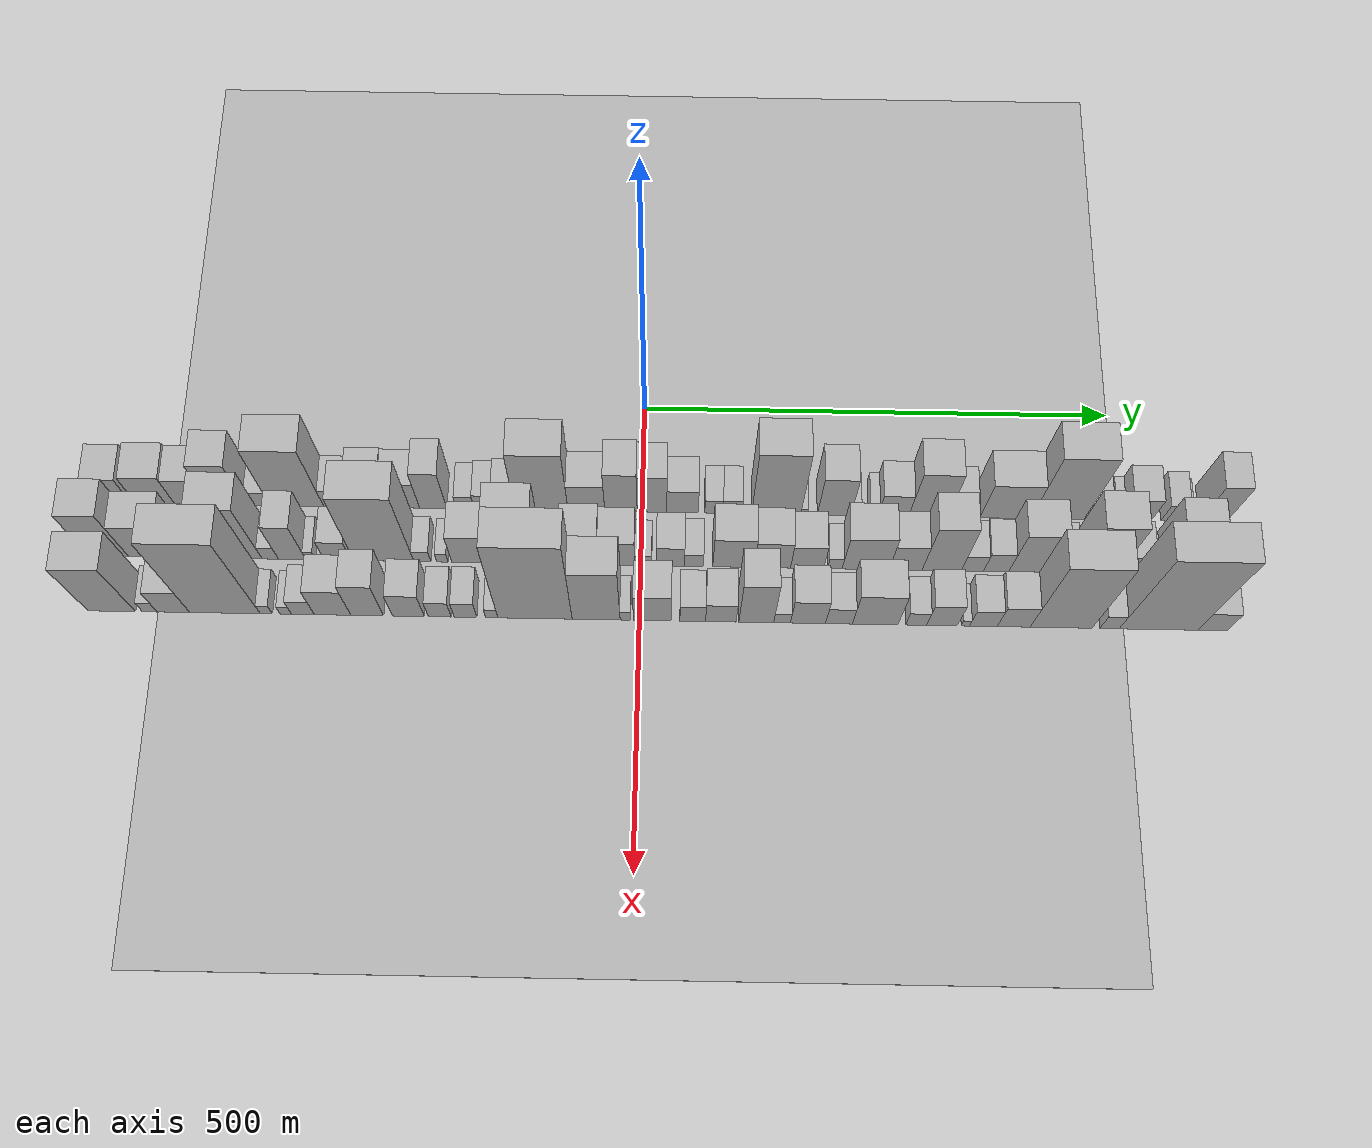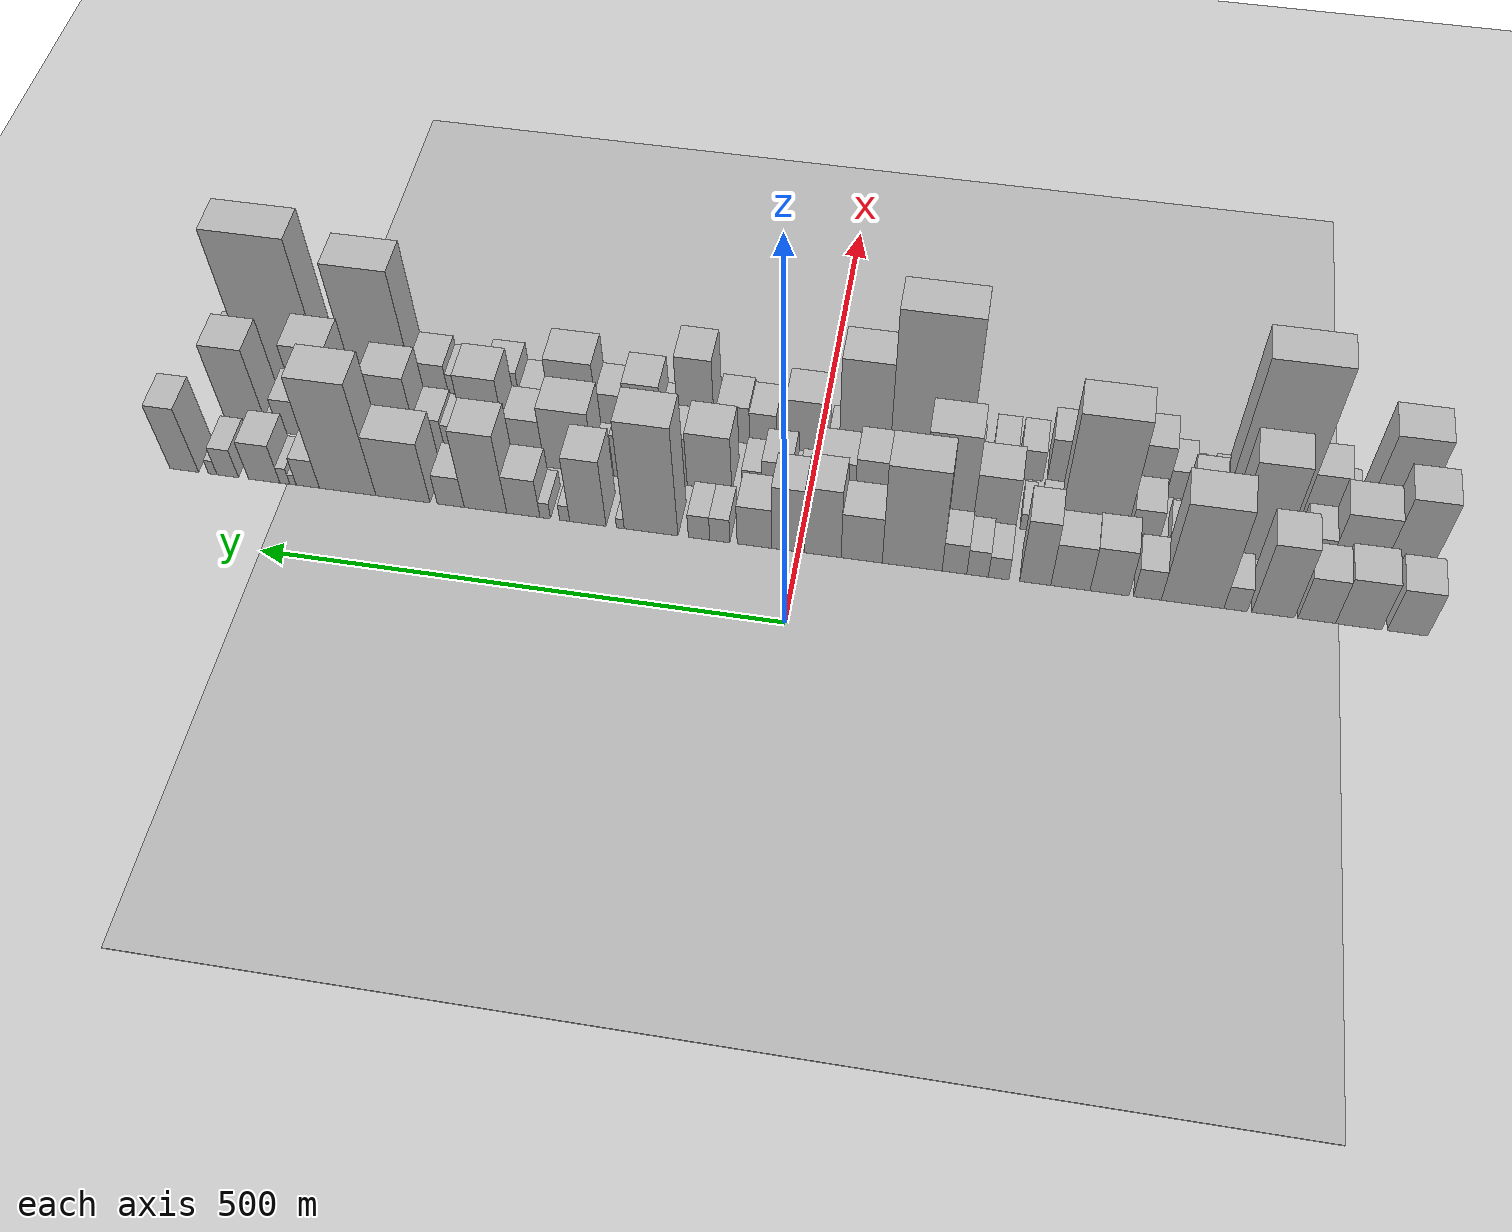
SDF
<?xml version="1.0" encoding="utf-8"?>

<sdf version="1.6">

   <world name="default">

      <gui fullscreen="0">

         <camera name="user_camera">

            <pose>-15 0 4.57585 0 0 0</pose>

            <view_controller>orbit</view_controller>

         </camera>

      </gui>

      <scene>

         <sky>

           <clouds>

             <speed>12</speed>

           </clouds>

         </sky>

         <ambient>0.4 0.4 0.4 1</ambient>

         <background>0.7 0.7 0.7 1</background>

         <shadows>1</shadows>

      </scene>

      <gravity>0 0 -9.8066</gravity>

      <magnetic_field>6e-06 2.3e-05 -4.2e-05</magnetic_field>

      <physics default="0" name="default_physics" type="ode">

         <ode>

            <solver>

               <type>quick</type>

               <iters>10</iters>

               <sor>1.0</sor>

               <use_dynamic_moi_rescaling>0</use_dynamic_moi_rescaling>

            </solver>

            <constraints>

               <cfm>0</cfm>

               <erp>0.2</erp>

               <contact_max_correcting_vel>100</contact_max_correcting_vel>

               <contact_surface_layer>0.001</contact_surface_layer>

            </constraints>

         </ode>

         <max_step_size>0.004</max_step_size>

         <real_time_factor>1</real_time_factor>

         <real_time_update_rate>250</real_time_update_rate>

      </physics>

      <light name="sun" type="directional">

         <cast_shadows>1</cast_shadows>

         <pose>0 0 10 0 0 0</pose>

         <diffuse>0.8 0.8 0.8 1</diffuse>

         <specular>0.2 0.2 0.2 1</specular>

         <attenuation>

            <range>1000</range>

            <constant>0.9</constant>

            <linear>0.01</linear>

            <quadratic>0.001</quadratic>

         </attenuation>

         <direction>-0.5 0.1 -0.9</direction>

      </light>

      <include>

         <name>ground_plane_1</name>

         <uri>model://HANNAS_ground_plane</uri>

         <pose>0 0 0  0 0 0</pose>

      </include>

      <include>

         <name>ground_plane_2</name>

         <uri>model://HANNAS_ground_plane</uri>

         <pose>100 0 0  0 0 0</pose>

      </include>

      <model name="building_1">

         <static>1</static>

         <pose frame="">100.0000 -561.8309 0 0.000000 0.000000 0.000000</pose>

         <link name="link">

            <pose frame="">0 0 33.00 0 0 0</pose>

            <collision name="collision">

               <geometry>

                  <box>

                     <size>40.0000 36.3382 66.0000</size>

                  </box>

               </geometry>

               <max_contacts>10</max_contacts>

               <surface>

                  <contact>

                     <ode/>

                  </contact>

                  <bounce/>

                  <friction>

                     <torsional>

                        <ode/>

                     </torsional>

                     <ode/>

                  </friction>

               </surface>

            </collision>

            <visual name="visual">

               <cast_shadows>0</cast_shadows>

               <geometry>

                  <box>

                     <size>40.0000 36.3382 66.0000</size>

                  </box>

               </geometry>

               <material>

                  <script>

                     <uri>model://HANNAS_wall/materials/scripts</uri>

                     <uri>model://HANNAS_wall/materials/textures</uri>

                     <name>vrc/HANNAS_wall</name>

                  </script>

               </material>

            </visual>

            <self_collide>0</self_collide>

            <enable_wind>0</enable_wind>

            <kinematic>0</kinematic>

         </link>

      </model>

      <model name="building_2">

         <static>1</static>

         <pose frame="">100.0000 -517.9481 0 0.000000 0.000000 0.000000</pose>

         <link name="link">

            <pose frame="">0 0 36.00 0 0 0</pose>

            <collision name="collision">

               <geometry>

                  <box>

                     <size>40.0000 41.4275 72.0000</size>

                  </box>

               </geometry>

               <max_contacts>10</max_contacts>

               <surface>

                  <contact>

                     <ode/>

                  </contact>

                  <bounce/>

                  <friction>

                     <torsional>

                        <ode/>

                     </torsional>

                     <ode/>

                  </friction>

               </surface>

            </collision>

            <visual name="visual">

               <cast_shadows>0</cast_shadows>

               <geometry>

                  <box>

                     <size>40.0000 41.4275 72.0000</size>

                  </box>

               </geometry>

               <material>

                  <script>

                     <uri>model://HANNAS_wall/materials/scripts</uri>

                     <uri>model://HANNAS_wall/materials/textures</uri>

                     <name>vrc/HANNAS_wall</name>

                  </script>

               </material>

            </visual>

            <self_collide>0</self_collide>

            <enable_wind>0</enable_wind>

            <kinematic>0</kinematic>

         </link>

      </model>

      <model name="building_3">

         <static>1</static>

         <pose frame="">100.0000 -480.1152 0 0.000000 0.000000 0.000000</pose>

         <link name="link">

            <pose frame="">0 0 33.00 0 0 0</pose>

            <collision name="collision">

               <geometry>

                  <box>

                     <size>40.0000 34.2383 66.0000</size>

                  </box>

               </geometry>

               <max_contacts>10</max_contacts>

               <surface>

                  <contact>

                     <ode/>

                  </contact>

                  <bounce/>

                  <friction>

                     <torsional>

                        <ode/>

                     </torsional>

                     <ode/>

                  </friction>

               </surface>

            </collision>

            <visual name="visual">

               <cast_shadows>0</cast_shadows>

               <geometry>

                  <box>

                     <size>40.0000 34.2383 66.0000</size>

                  </box>

               </geometry>

               <material>

                  <script>

                     <uri>model://HANNAS_wall/materials/scripts</uri>

                     <uri>model://HANNAS_wall/materials/textures</uri>

                     <name>vrc/HANNAS_wall</name>

                  </script>

               </material>

            </visual>

            <self_collide>0</self_collide>

            <enable_wind>0</enable_wind>

            <kinematic>0</kinematic>

         </link>

      </model>

      <model name="building_4">

         <static>1</static>

         <pose frame="">100.0000 -440.6088 0 0.000000 0.000000 0.000000</pose>

         <link name="link">

            <pose frame="">0 0 54.00 0 0 0</pose>

            <collision name="collision">

               <geometry>

                  <box>

                     <size>40.0000 38.7744 108.0000</size>

                  </box>

               </geometry>

               <max_contacts>10</max_contacts>

               <surface>

                  <contact>

                     <ode/>

                  </contact>

                  <bounce/>

                  <friction>

                     <torsional>

                        <ode/>

                     </torsional>

                     <ode/>

                  </friction>

               </surface>

            </collision>

            <visual name="visual">

               <cast_shadows>0</cast_shadows>

               <geometry>

                  <box>

                     <size>40.0000 38.7744 108.0000</size>

                  </box>

               </geometry>

               <material>

                  <script>

                     <uri>model://HANNAS_wall/materials/scripts</uri>

                     <uri>model://HANNAS_wall/materials/textures</uri>

                     <name>vrc/HANNAS_wall</name>

                  </script>

               </material>

            </visual>

            <self_collide>0</self_collide>

            <enable_wind>0</enable_wind>

            <kinematic>0</kinematic>

         </link>

      </model>

      <model name="building_5">

         <static>1</static>

         <pose frame="">100.0000 -406.5077 0 0.000000 0.000000 0.000000</pose>

         <link name="link">

            <pose frame="">0 0 18.00 0 0 0</pose>

            <collision name="collision">

               <geometry>

                  <box>

                     <size>40.0000 21.4278 36.0000</size>

                  </box>

               </geometry>

               <max_contacts>10</max_contacts>

               <surface>

                  <contact>

                     <ode/>

                  </contact>

                  <bounce/>

                  <friction>

                     <torsional>

                        <ode/>

                     </torsional>

                     <ode/>

                  </friction>

               </surface>

            </collision>

            <visual name="visual">

               <cast_shadows>0</cast_shadows>

               <geometry>

                  <box>

                     <size>40.0000 21.4278 36.0000</size>

                  </box>

               </geometry>

               <material>

                  <script>

                     <uri>model://HANNAS_wall/materials/scripts</uri>

                     <uri>model://HANNAS_wall/materials/textures</uri>

                     <name>vrc/HANNAS_wall</name>

                  </script>

               </material>

            </visual>

            <self_collide>0</self_collide>

            <enable_wind>0</enable_wind>

            <kinematic>0</kinematic>

         </link>

      </model>

      <model name="building_6">

         <static>1</static>

         <pose frame="">100.0000 -367.1840 0 0.000000 0.000000 0.000000</pose>

         <link name="link">

            <pose frame="">0 0 75.00 0 0 0</pose>

            <collision name="collision">

               <geometry>

                  <box>

                     <size>40.0000 57.2195 150.0000</size>

                  </box>

               </geometry>

               <max_contacts>10</max_contacts>

               <surface>

                  <contact>

                     <ode/>

                  </contact>

                  <bounce/>

                  <friction>

                     <torsional>

                        <ode/>

                     </torsional>

                     <ode/>

                  </friction>

               </surface>

            </collision>

            <visual name="visual">

               <cast_shadows>0</cast_shadows>

               <geometry>

                  <box>

                     <size>40.0000 57.2195 150.0000</size>

                  </box>

               </geometry>

               <material>

                  <script>

                     <uri>model://HANNAS_wall/materials/scripts</uri>

                     <uri>model://HANNAS_wall/materials/textures</uri>

                     <name>vrc/HANNAS_wall</name>

                  </script>

               </material>

            </visual>

            <self_collide>0</self_collide>

            <enable_wind>0</enable_wind>

            <kinematic>0</kinematic>

         </link>

      </model>

      <model name="building_7">

         <static>1</static>

         <pose frame="">100.0000 -325.8104 0 0.000000 0.000000 0.000000</pose>

         <link name="link">

            <pose frame="">0 0 22.50 0 0 0</pose>

            <collision name="collision">

               <geometry>

                  <box>

                     <size>40.0000 25.5277 45.0000</size>

                  </box>

               </geometry>

               <max_contacts>10</max_contacts>

               <surface>

                  <contact>

                     <ode/>

                  </contact>

                  <bounce/>

                  <friction>

                     <torsional>

                        <ode/>

                     </torsional>

                     <ode/>

                  </friction>

               </surface>

            </collision>

            <visual name="visual">

               <cast_shadows>0</cast_shadows>

               <geometry>

                  <box>

                     <size>40.0000 25.5277 45.0000</size>

                  </box>

               </geometry>

               <material>

                  <script>

                     <uri>model://HANNAS_wall/materials/scripts</uri>

                     <uri>model://HANNAS_wall/materials/textures</uri>

                     <name>vrc/HANNAS_wall</name>

                  </script>

               </material>

            </visual>

            <self_collide>0</self_collide>

            <enable_wind>0</enable_wind>

            <kinematic>0</kinematic>

         </link>

      </model>

      <model name="building_8">

         <static>1</static>

         <pose frame="">100.0000 -291.0160 0 0.000000 0.000000 0.000000</pose>

         <link name="link">

            <pose frame="">0 0 34.50 0 0 0</pose>

            <collision name="collision">

               <geometry>

                  <box>

                     <size>40.0000 36.0610 69.0000</size>

                  </box>

               </geometry>

               <max_contacts>10</max_contacts>

               <surface>

                  <contact>

                     <ode/>

                  </contact>

                  <bounce/>

                  <friction>

                     <torsional>

                        <ode/>

                     </torsional>

                     <ode/>

                  </friction>

               </surface>

            </collision>

            <visual name="visual">

               <cast_shadows>0</cast_shadows>

               <geometry>

                  <box>

                     <size>40.0000 36.0610 69.0000</size>

                  </box>

               </geometry>

               <material>

                  <script>

                     <uri>model://HANNAS_wall/materials/scripts</uri>

                     <uri>model://HANNAS_wall/materials/textures</uri>

                     <name>vrc/HANNAS_wall</name>

                  </script>

               </material>

            </visual>

            <self_collide>0</self_collide>

            <enable_wind>0</enable_wind>

            <kinematic>0</kinematic>

         </link>

      </model>

      <model name="building_9">

         <static>1</static>

         <pose frame="">100.0000 -254.7991 0 0.000000 0.000000 0.000000</pose>

         <link name="link">

            <pose frame="">0 0 33.00 0 0 0</pose>

            <collision name="collision">

               <geometry>

                  <box>

                     <size>40.0000 36.3728 66.0000</size>

                  </box>

               </geometry>

               <max_contacts>10</max_contacts>

               <surface>

                  <contact>

                     <ode/>

                  </contact>

                  <bounce/>

                  <friction>

                     <torsional>

                        <ode/>

                     </torsional>

                     <ode/>

                  </friction>

               </surface>

            </collision>

            <visual name="visual">

               <cast_shadows>0</cast_shadows>

               <geometry>

                  <box>

                     <size>40.0000 36.3728 66.0000</size>

                  </box>

               </geometry>

               <material>

                  <script>

                     <uri>model://HANNAS_wall/materials/scripts</uri>

                     <uri>model://HANNAS_wall/materials/textures</uri>

                     <name>vrc/HANNAS_wall</name>

                  </script>

               </material>

            </visual>

            <self_collide>0</self_collide>

            <enable_wind>0</enable_wind>

            <kinematic>0</kinematic>

         </link>

      </model>

      <model name="building_10">

         <static>1</static>

         <pose frame="">100.0000 -222.1280 0 0.000000 0.000000 0.000000</pose>

         <link name="link">

            <pose frame="">0 0 48.00 0 0 0</pose>

            <collision name="collision">

               <geometry>

                  <box>

                     <size>40.0000 28.9694 96.0000</size>

                  </box>

               </geometry>

               <max_contacts>10</max_contacts>

               <surface>

                  <contact>

                     <ode/>

                  </contact>

                  <bounce/>

                  <friction>

                     <torsional>

                        <ode/>

                     </torsional>

                     <ode/>

                  </friction>

               </surface>

            </collision>

            <visual name="visual">

               <cast_shadows>0</cast_shadows>

               <geometry>

                  <box>

                     <size>40.0000 28.9694 96.0000</size>

                  </box>

               </geometry>

               <material>

                  <script>

                     <uri>model://HANNAS_wall/materials/scripts</uri>

                     <uri>model://HANNAS_wall/materials/textures</uri>

                     <name>vrc/HANNAS_wall</name>

                  </script>

               </material>

            </visual>

            <self_collide>0</self_collide>

            <enable_wind>0</enable_wind>

            <kinematic>0</kinematic>

         </link>

      </model>

      <model name="building_11">

         <static>1</static>

         <pose frame="">100.0000 -188.0623 0 0.000000 0.000000 0.000000</pose>

         <link name="link">

            <pose frame="">0 0 16.50 0 0 0</pose>

            <collision name="collision">

               <geometry>

                  <box>

                     <size>40.0000 19.1621 33.0000</size>

                  </box>

               </geometry>

               <max_contacts>10</max_contacts>

               <surface>

                  <contact>

                     <ode/>

                  </contact>

                  <bounce/>

                  <friction>

                     <torsional>

                        <ode/>

                     </torsional>

                     <ode/>

                  </friction>

               </surface>

            </collision>

            <visual name="visual">

               <cast_shadows>0</cast_shadows>

               <geometry>

                  <box>

                     <size>40.0000 19.1621 33.0000</size>

                  </box>

               </geometry>

               <material>

                  <script>

                     <uri>model://HANNAS_wall/materials/scripts</uri>

                     <uri>model://HANNAS_wall/materials/textures</uri>

                     <name>vrc/HANNAS_wall</name>

                  </script>

               </material>

            </visual>

            <self_collide>0</self_collide>

            <enable_wind>0</enable_wind>

            <kinematic>0</kinematic>

         </link>

      </model>

      <model name="building_12">

         <static>1</static>

         <pose frame="">100.0000 -168.3944 0 0.000000 0.000000 0.000000</pose>

         <link name="link">

            <pose frame="">0 0 19.50 0 0 0</pose>

            <collision name="collision">

               <geometry>

                  <box>

                     <size>40.0000 20.1737 39.0000</size>

                  </box>

               </geometry>

               <max_contacts>10</max_contacts>

               <surface>

                  <contact>

                     <ode/>

                  </contact>

                  <bounce/>

                  <friction>

                     <torsional>

                        <ode/>

                     </torsional>

                     <ode/>

                  </friction>

               </surface>

            </collision>

            <visual name="visual">

               <cast_shadows>0</cast_shadows>

               <geometry>

                  <box>

                     <size>40.0000 20.1737 39.0000</size>

                  </box>

               </geometry>

               <material>

                  <script>

                     <uri>model://HANNAS_wall/materials/scripts</uri>

                     <uri>model://HANNAS_wall/materials/textures</uri>

                     <name>vrc/HANNAS_wall</name>

                  </script>

               </material>

            </visual>

            <self_collide>0</self_collide>

            <enable_wind>0</enable_wind>

            <kinematic>0</kinematic>

         </link>

      </model>

      <model name="building_13">

         <static>1</static>

         <pose frame="">100.0000 -146.7684 0 0.000000 0.000000 0.000000</pose>

         <link name="link">

            <pose frame="">0 0 22.50 0 0 0</pose>

            <collision name="collision">

               <geometry>

                  <box>

                     <size>40.0000 23.0784 45.0000</size>

                  </box>

               </geometry>

               <max_contacts>10</max_contacts>

               <surface>

                  <contact>

                     <ode/>

                  </contact>

                  <bounce/>

                  <friction>

                     <torsional>

                        <ode/>

                     </torsional>

                     <ode/>

                  </friction>

               </surface>

            </collision>

            <visual name="visual">

               <cast_shadows>0</cast_shadows>

               <geometry>

                  <box>

                     <size>40.0000 23.0784 45.0000</size>

                  </box>

               </geometry>

               <material>

                  <script>

                     <uri>model://HANNAS_wall/materials/scripts</uri>

                     <uri>model://HANNAS_wall/materials/textures</uri>

                     <name>vrc/HANNAS_wall</name>

                  </script>

               </material>

            </visual>

            <self_collide>0</self_collide>

            <enable_wind>0</enable_wind>

            <kinematic>0</kinematic>

         </link>

      </model>

      <model name="building_14">

         <static>1</static>

         <pose frame="">100.0000 -107.0649 0 0.000000 0.000000 0.000000</pose>

         <link name="link">

            <pose frame="">0 0 75.00 0 0 0</pose>

            <collision name="collision">

               <geometry>

                  <box>

                     <size>40.0000 56.3285 150.0000</size>

                  </box>

               </geometry>

               <max_contacts>10</max_contacts>

               <surface>

                  <contact>

                     <ode/>

                  </contact>

                  <bounce/>

                  <friction>

                     <torsional>

                        <ode/>

                     </torsional>

                     <ode/>

                  </friction>

               </surface>

            </collision>

            <visual name="visual">

               <cast_shadows>0</cast_shadows>

               <geometry>

                  <box>

                     <size>40.0000 56.3285 150.0000</size>

                  </box>

               </geometry>

               <material>

                  <script>

                     <uri>model://HANNAS_wall/materials/scripts</uri>

                     <uri>model://HANNAS_wall/materials/textures</uri>

                     <name>vrc/HANNAS_wall</name>

                  </script>

               </material>

            </visual>

            <self_collide>0</self_collide>

            <enable_wind>0</enable_wind>

            <kinematic>0</kinematic>

         </link>

      </model>

      <model name="building_15">

         <static>1</static>

         <pose frame="">100.0000 -59.4415 0 0.000000 0.000000 0.000000</pose>

         <link name="link">

            <pose frame="">0 0 34.50 0 0 0</pose>

            <collision name="collision">

               <geometry>

                  <box>

                     <size>40.0000 38.9183 69.0000</size>

                  </box>

               </geometry>

               <max_contacts>10</max_contacts>

               <surface>

                  <contact>

                     <ode/>

                  </contact>

                  <bounce/>

                  <friction>

                     <torsional>

                        <ode/>

                     </torsional>

                     <ode/>

                  </friction>

               </surface>

            </collision>

            <visual name="visual">

               <cast_shadows>0</cast_shadows>

               <geometry>

                  <box>

                     <size>40.0000 38.9183 69.0000</size>

                  </box>

               </geometry>

               <material>

                  <script>

                     <uri>model://HANNAS_wall/materials/scripts</uri>

                     <uri>model://HANNAS_wall/materials/textures</uri>

                     <name>vrc/HANNAS_wall</name>

                  </script>

               </material>

            </visual>

            <self_collide>0</self_collide>

            <enable_wind>0</enable_wind>

            <kinematic>0</kinematic>

         </link>

      </model>

      <model name="building_16">

         <static>1</static>

         <pose frame="">100.0000 -22.7742 0 0.000000 0.000000 0.000000</pose>

         <link name="link">

            <pose frame="">0 0 51.00 0 0 0</pose>

            <collision name="collision">

               <geometry>

                  <box>

                     <size>40.0000 34.4164 102.0000</size>

                  </box>

               </geometry>

               <max_contacts>10</max_contacts>

               <surface>

                  <contact>

                     <ode/>

                  </contact>

                  <bounce/>

                  <friction>

                     <torsional>

                        <ode/>

                     </torsional>

                     <ode/>

                  </friction>

               </surface>

            </collision>

            <visual name="visual">

               <cast_shadows>0</cast_shadows>

               <geometry>

                  <box>

                     <size>40.0000 34.4164 102.0000</size>

                  </box>

               </geometry>

               <material>

                  <script>

                     <uri>model://HANNAS_wall/materials/scripts</uri>

                     <uri>model://HANNAS_wall/materials/textures</uri>

                     <name>vrc/HANNAS_wall</name>

                  </script>

               </material>

            </visual>

            <self_collide>0</self_collide>

            <enable_wind>0</enable_wind>

            <kinematic>0</kinematic>

         </link>

      </model>

      <model name="building_17">

         <static>1</static>

         <pose frame="">100.0000 10.1270 0 0.000000 0.000000 0.000000</pose>

         <link name="link">

            <pose frame="">0 0 48.00 0 0 0</pose>

            <collision name="collision">

               <geometry>

                  <box>

                     <size>40.0000 31.3859 96.0000</size>

                  </box>

               </geometry>

               <max_contacts>10</max_contacts>

               <surface>

                  <contact>

                     <ode/>

                  </contact>

                  <bounce/>

                  <friction>

                     <torsional>

                        <ode/>

                     </torsional>

                     <ode/>

                  </friction>

               </surface>

            </collision>

            <visual name="visual">

               <cast_shadows>0</cast_shadows>

               <geometry>

                  <box>

                     <size>40.0000 31.3859 96.0000</size>

                  </box>

               </geometry>

               <material>

                  <script>

                     <uri>model://HANNAS_wall/materials/scripts</uri>

                     <uri>model://HANNAS_wall/materials/textures</uri>

                     <name>vrc/HANNAS_wall</name>

                  </script>

               </material>

            </visual>

            <self_collide>0</self_collide>

            <enable_wind>0</enable_wind>

            <kinematic>0</kinematic>

         </link>

      </model>

      <model name="building_18">

         <static>1</static>

         <pose frame="">100.0000 42.4086 0 0.000000 0.000000 0.000000</pose>

         <link name="link">

            <pose frame="">0 0 30.00 0 0 0</pose>

            <collision name="collision">

               <geometry>

                  <box>

                     <size>40.0000 33.1775 60.0000</size>

                  </box>

               </geometry>

               <max_contacts>10</max_contacts>

               <surface>

                  <contact>

                     <ode/>

                  </contact>

                  <bounce/>

                  <friction>

                     <torsional>

                        <ode/>

                     </torsional>

                     <ode/>

                  </friction>

               </surface>

            </collision>

            <visual name="visual">

               <cast_shadows>0</cast_shadows>

               <geometry>

                  <box>

                     <size>40.0000 33.1775 60.0000</size>

                  </box>

               </geometry>

               <material>

                  <script>

                     <uri>model://HANNAS_wall/materials/scripts</uri>

                     <uri>model://HANNAS_wall/materials/textures</uri>

                     <name>vrc/HANNAS_wall</name>

                  </script>

               </material>

            </visual>

            <self_collide>0</self_collide>

            <enable_wind>0</enable_wind>

            <kinematic>0</kinematic>

         </link>

      </model>

      <model name="building_19">

         <static>1</static>

         <pose frame="">100.0000 75.5982 0 0.000000 0.000000 0.000000</pose>

         <link name="link">

            <pose frame="">0 0 18.00 0 0 0</pose>

            <collision name="collision">

               <geometry>

                  <box>

                     <size>40.0000 19.2016 36.0000</size>

                  </box>

               </geometry>

               <max_contacts>10</max_contacts>

               <surface>

                  <contact>

                     <ode/>

                  </contact>

                  <bounce/>

                  <friction>

                     <torsional>

                        <ode/>

                     </torsional>

                     <ode/>

                  </friction>

               </surface>

            </collision>

            <visual name="visual">

               <cast_shadows>0</cast_shadows>

               <geometry>

                  <box>

                     <size>40.0000 19.2016 36.0000</size>

                  </box>

               </geometry>

               <material>

                  <script>

                     <uri>model://HANNAS_wall/materials/scripts</uri>

                     <uri>model://HANNAS_wall/materials/textures</uri>

                     <name>vrc/HANNAS_wall</name>

                  </script>

               </material>

            </visual>

            <self_collide>0</self_collide>

            <enable_wind>0</enable_wind>

            <kinematic>0</kinematic>

         </link>

      </model>

      <model name="building_20">

         <static>1</static>

         <pose frame="">100.0000 95.5008 0 0.000000 0.000000 0.000000</pose>

         <link name="link">

            <pose frame="">0 0 18.00 0 0 0</pose>

            <collision name="collision">

               <geometry>

                  <box>

                     <size>40.0000 20.6037 36.0000</size>

                  </box>

               </geometry>

               <max_contacts>10</max_contacts>

               <surface>

                  <contact>

                     <ode/>

                  </contact>

                  <bounce/>

                  <friction>

                     <torsional>

                        <ode/>

                     </torsional>

                     <ode/>

                  </friction>

               </surface>

            </collision>

            <visual name="visual">

               <cast_shadows>0</cast_shadows>

               <geometry>

                  <box>

                     <size>40.0000 20.6037 36.0000</size>

                  </box>

               </geometry>

               <material>

                  <script>

                     <uri>model://HANNAS_wall/materials/scripts</uri>

                     <uri>model://HANNAS_wall/materials/textures</uri>

                     <name>vrc/HANNAS_wall</name>

                  </script>

               </material>

            </visual>

            <self_collide>0</self_collide>

            <enable_wind>0</enable_wind>

            <kinematic>0</kinematic>

         </link>

      </model>

      <model name="building_21">

         <static>1</static>

         <pose frame="">100.0000 141.8092 0 0.000000 0.000000 0.000000</pose>

         <link name="link">

            <pose frame="">0 0 81.00 0 0 0</pose>

            <collision name="collision">

               <geometry>

                  <box>

                     <size>40.0000 52.0130 162.0000</size>

                  </box>

               </geometry>

               <max_contacts>10</max_contacts>

               <surface>

                  <contact>

                     <ode/>

                  </contact>

                  <bounce/>

                  <friction>

                     <torsional>

                        <ode/>

                     </torsional>

                     <ode/>

                  </friction>

               </surface>

            </collision>

            <visual name="visual">

               <cast_shadows>0</cast_shadows>

               <geometry>

                  <box>

                     <size>40.0000 52.0130 162.0000</size>

                  </box>

               </geometry>

               <material>

                  <script>

                     <uri>model://HANNAS_wall/materials/scripts</uri>

                     <uri>model://HANNAS_wall/materials/textures</uri>

                     <name>vrc/HANNAS_wall</name>

                  </script>

               </material>

            </visual>

            <self_collide>0</self_collide>

            <enable_wind>0</enable_wind>

            <kinematic>0</kinematic>

         </link>

      </model>

      <model name="building_22">

         <static>1</static>

         <pose frame="">100.0000 171.5599 0 0.000000 0.000000 0.000000</pose>

         <link name="link">

            <pose frame="">0 0 7.50 0 0 0</pose>

            <collision name="collision">

               <geometry>

                  <box>

                     <size>40.0000 7.4884 15.0000</size>

                  </box>

               </geometry>

               <max_contacts>10</max_contacts>

               <surface>

                  <contact>

                     <ode/>

                  </contact>

                  <bounce/>

                  <friction>

                     <torsional>

                        <ode/>

                     </torsional>

                     <ode/>

                  </friction>

               </surface>

            </collision>

            <visual name="visual">

               <cast_shadows>0</cast_shadows>

               <geometry>

                  <box>

                     <size>40.0000 7.4884 15.0000</size>

                  </box>

               </geometry>

               <material>

                  <script>

                     <uri>model://HANNAS_wall/materials/scripts</uri>

                     <uri>model://HANNAS_wall/materials/textures</uri>

                     <name>vrc/HANNAS_wall</name>

                  </script>

               </material>

            </visual>

            <self_collide>0</self_collide>

            <enable_wind>0</enable_wind>

            <kinematic>0</kinematic>

         </link>

      </model>

      <model name="building_23">

         <static>1</static>

         <pose frame="">100.0000 203.0476 0 0.000000 0.000000 0.000000</pose>

         <link name="link">

            <pose frame="">0 0 49.50 0 0 0</pose>

            <collision name="collision">

               <geometry>

                  <box>

                     <size>40.0000 35.4869 99.0000</size>

                  </box>

               </geometry>

               <max_contacts>10</max_contacts>

               <surface>

                  <contact>

                     <ode/>

                  </contact>

                  <bounce/>

                  <friction>

                     <torsional>

                        <ode/>

                     </torsional>

                     <ode/>

                  </friction>

               </surface>

            </collision>

            <visual name="visual">

               <cast_shadows>0</cast_shadows>

               <geometry>

                  <box>

                     <size>40.0000 35.4869 99.0000</size>

                  </box>

               </geometry>

               <material>

                  <script>

                     <uri>model://HANNAS_wall/materials/scripts</uri>

                     <uri>model://HANNAS_wall/materials/textures</uri>

                     <name>vrc/HANNAS_wall</name>

                  </script>

               </material>

            </visual>

            <self_collide>0</self_collide>

            <enable_wind>0</enable_wind>

            <kinematic>0</kinematic>

         </link>

      </model>

      <model name="building_24">

         <static>1</static>

         <pose frame="">100.0000 225.6169 0 0.000000 0.000000 0.000000</pose>

         <link name="link">

            <pose frame="">0 0 12.00 0 0 0</pose>

            <collision name="collision">

               <geometry>

                  <box>

                     <size>40.0000 9.6518 24.0000</size>

                  </box>

               </geometry>

               <max_contacts>10</max_contacts>

               <surface>

                  <contact>

                     <ode/>

                  </contact>

                  <bounce/>

                  <friction>

                     <torsional>

                        <ode/>

                     </torsional>

                     <ode/>

                  </friction>

               </surface>

            </collision>

            <visual name="visual">

               <cast_shadows>0</cast_shadows>

               <geometry>

                  <box>

                     <size>40.0000 9.6518 24.0000</size>

                  </box>

               </geometry>

               <material>

                  <script>

                     <uri>model://HANNAS_wall/materials/scripts</uri>

                     <uri>model://HANNAS_wall/materials/textures</uri>

                     <name>vrc/HANNAS_wall</name>

                  </script>

               </material>

            </visual>

            <self_collide>0</self_collide>

            <enable_wind>0</enable_wind>

            <kinematic>0</kinematic>

         </link>

      </model>

      <model name="building_25">

         <static>1</static>

         <pose frame="">100.0000 244.6090 0 0.000000 0.000000 0.000000</pose>

         <link name="link">

            <pose frame="">0 0 12.00 0 0 0</pose>

            <collision name="collision">

               <geometry>

                  <box>

                     <size>40.0000 10.3324 24.0000</size>

                  </box>

               </geometry>

               <max_contacts>10</max_contacts>

               <surface>

                  <contact>

                     <ode/>

                  </contact>

                  <bounce/>

                  <friction>

                     <torsional>

                        <ode/>

                     </torsional>

                     <ode/>

                  </friction>

               </surface>

            </collision>

            <visual name="visual">

               <cast_shadows>0</cast_shadows>

               <geometry>

                  <box>

                     <size>40.0000 10.3324 24.0000</size>

                  </box>

               </geometry>

               <material>

                  <script>

                     <uri>model://HANNAS_wall/materials/scripts</uri>

                     <uri>model://HANNAS_wall/materials/textures</uri>

                     <name>vrc/HANNAS_wall</name>

                  </script>

               </material>

            </visual>

            <self_collide>0</self_collide>

            <enable_wind>0</enable_wind>

            <kinematic>0</kinematic>

         </link>

      </model>

      <model name="building_26">

         <static>1</static>

         <pose frame="">100.0000 265.9587 0 0.000000 0.000000 0.000000</pose>

         <link name="link">

            <pose frame="">0 0 28.50 0 0 0</pose>

            <collision name="collision">

               <geometry>

                  <box>

                     <size>40.0000 32.3671 57.0000</size>

                  </box>

               </geometry>

               <max_contacts>10</max_contacts>

               <surface>

                  <contact>

                     <ode/>

                  </contact>

                  <bounce/>

                  <friction>

                     <torsional>

                        <ode/>

                     </torsional>

                     <ode/>

                  </friction>

               </surface>

            </collision>

            <visual name="visual">

               <cast_shadows>0</cast_shadows>

               <geometry>

                  <box>

                     <size>40.0000 32.3671 57.0000</size>

                  </box>

               </geometry>

               <material>

                  <script>

                     <uri>model://HANNAS_wall/materials/scripts</uri>

                     <uri>model://HANNAS_wall/materials/textures</uri>

                     <name>vrc/HANNAS_wall</name>

                  </script>

               </material>

            </visual>

            <self_collide>0</self_collide>

            <enable_wind>0</enable_wind>

            <kinematic>0</kinematic>

         </link>

      </model>

      <model name="building_27">

         <static>1</static>

         <pose frame="">100.0000 303.1173 0 0.000000 0.000000 0.000000</pose>

         <link name="link">

            <pose frame="">0 0 58.50 0 0 0</pose>

            <collision name="collision">

               <geometry>

                  <box>

                     <size>40.0000 41.9502 117.0000</size>

                  </box>

               </geometry>

               <max_contacts>10</max_contacts>

               <surface>

                  <contact>

                     <ode/>

                  </contact>

                  <bounce/>

                  <friction>

                     <torsional>

                        <ode/>

                     </torsional>

                     <ode/>

                  </friction>

               </surface>

            </collision>

            <visual name="visual">

               <cast_shadows>0</cast_shadows>

               <geometry>

                  <box>

                     <size>40.0000 41.9502 117.0000</size>

                  </box>

               </geometry>

               <material>

                  <script>

                     <uri>model://HANNAS_wall/materials/scripts</uri>

                     <uri>model://HANNAS_wall/materials/textures</uri>

                     <name>vrc/HANNAS_wall</name>

                  </script>

               </material>

            </visual>

            <self_collide>0</self_collide>

            <enable_wind>0</enable_wind>

            <kinematic>0</kinematic>

         </link>

      </model>

      <model name="building_28">

         <static>1</static>

         <pose frame="">100.0000 337.4223 0 0.000000 0.000000 0.000000</pose>

         <link name="link">

            <pose frame="">0 0 22.50 0 0 0</pose>

            <collision name="collision">

               <geometry>

                  <box>

                     <size>40.0000 26.6598 45.0000</size>

                  </box>

               </geometry>

               <max_contacts>10</max_contacts>

               <surface>

                  <contact>

                     <ode/>

                  </contact>

                  <bounce/>

                  <friction>

                     <torsional>

                        <ode/>

                     </torsional>

                     <ode/>

                  </friction>

               </surface>

            </collision>

            <visual name="visual">

               <cast_shadows>0</cast_shadows>

               <geometry>

                  <box>

                     <size>40.0000 26.6598 45.0000</size>

                  </box>

               </geometry>

               <material>

                  <script>

                     <uri>model://HANNAS_wall/materials/scripts</uri>

                     <uri>model://HANNAS_wall/materials/textures</uri>

                     <name>vrc/HANNAS_wall</name>

                  </script>

               </material>

            </visual>

            <self_collide>0</self_collide>

            <enable_wind>0</enable_wind>

            <kinematic>0</kinematic>

         </link>

      </model>

      <model name="building_29">

         <static>1</static>

         <pose frame="">100.0000 384.5578 0 0.000000 0.000000 0.000000</pose>

         <link name="link">

            <pose frame="">0 0 45.00 0 0 0</pose>

            <collision name="collision">

               <geometry>

                  <box>

                     <size>40.0000 53.6112 90.0000</size>

                  </box>

               </geometry>

               <max_contacts>10</max_contacts>

               <surface>

                  <contact>

                     <ode/>

                  </contact>

                  <bounce/>

                  <friction>

                     <torsional>

                        <ode/>

                     </torsional>

                     <ode/>

                  </friction>

               </surface>

            </collision>

            <visual name="visual">

               <cast_shadows>0</cast_shadows>

               <geometry>

                  <box>

                     <size>40.0000 53.6112 90.0000</size>

                  </box>

               </geometry>

               <material>

                  <script>

                     <uri>model://HANNAS_wall/materials/scripts</uri>

                     <uri>model://HANNAS_wall/materials/textures</uri>

                     <name>vrc/HANNAS_wall</name>

                  </script>

               </material>

            </visual>

            <self_collide>0</self_collide>

            <enable_wind>0</enable_wind>

            <kinematic>0</kinematic>

         </link>

      </model>

      <model name="building_30">

         <static>1</static>

         <pose frame="">100.0000 439.6174 0 0.000000 0.000000 0.000000</pose>

         <link name="link">

            <pose frame="">0 0 82.50 0 0 0</pose>

            <collision name="collision">

               <geometry>

                  <box>

                     <size>40.0000 56.5080 165.0000</size>

                  </box>

               </geometry>

               <max_contacts>10</max_contacts>

               <surface>

                  <contact>

                     <ode/>

                  </contact>

                  <bounce/>

                  <friction>

                     <torsional>

                        <ode/>

                     </torsional>

                     <ode/>

                  </friction>

               </surface>

            </collision>

            <visual name="visual">

               <cast_shadows>0</cast_shadows>

               <geometry>

                  <box>

                     <size>40.0000 56.5080 165.0000</size>

                  </box>

               </geometry>

               <material>

                  <script>

                     <uri>model://HANNAS_wall/materials/scripts</uri>

                     <uri>model://HANNAS_wall/materials/textures</uri>

                     <name>vrc/HANNAS_wall</name>

                  </script>

               </material>

            </visual>

            <self_collide>0</self_collide>

            <enable_wind>0</enable_wind>

            <kinematic>0</kinematic>

         </link>

      </model>

      <model name="building_31">

         <static>1</static>

         <pose frame="">100.0000 479.4380 0 0.000000 0.000000 0.000000</pose>

         <link name="link">

            <pose frame="">0 0 21.00 0 0 0</pose>

            <collision name="collision">

               <geometry>

                  <box>

                     <size>40.0000 23.1332 42.0000</size>

                  </box>

               </geometry>

               <max_contacts>10</max_contacts>

               <surface>

                  <contact>

                     <ode/>

                  </contact>

                  <bounce/>

                  <friction>

                     <torsional>

                        <ode/>

                     </torsional>

                     <ode/>

                  </friction>

               </surface>

            </collision>

            <visual name="visual">

               <cast_shadows>0</cast_shadows>

               <geometry>

                  <box>

                     <size>40.0000 23.1332 42.0000</size>

                  </box>

               </geometry>

               <material>

                  <script>

                     <uri>model://HANNAS_wall/materials/scripts</uri>

                     <uri>model://HANNAS_wall/materials/textures</uri>

                     <name>vrc/HANNAS_wall</name>

                  </script>

               </material>

            </visual>

            <self_collide>0</self_collide>

            <enable_wind>0</enable_wind>

            <kinematic>0</kinematic>

         </link>

      </model>

      <model name="building_32">

         <static>1</static>

         <pose frame="">100.0000 494.2023 0 0.000000 0.000000 0.000000</pose>

         <link name="link">

            <pose frame="">0 0 7.50 0 0 0</pose>

            <collision name="collision">

               <geometry>

                  <box>

                     <size>40.0000 6.3954 15.0000</size>

                  </box>

               </geometry>

               <max_contacts>10</max_contacts>

               <surface>

                  <contact>

                     <ode/>

                  </contact>

                  <bounce/>

                  <friction>

                     <torsional>

                        <ode/>

                     </torsional>

                     <ode/>

                  </friction>

               </surface>

            </collision>

            <visual name="visual">

               <cast_shadows>0</cast_shadows>

               <geometry>

                  <box>

                     <size>40.0000 6.3954 15.0000</size>

                  </box>

               </geometry>

               <material>

                  <script>

                     <uri>model://HANNAS_wall/materials/scripts</uri>

                     <uri>model://HANNAS_wall/materials/textures</uri>

                     <name>vrc/HANNAS_wall</name>

                  </script>

               </material>

            </visual>

            <self_collide>0</self_collide>

            <enable_wind>0</enable_wind>

            <kinematic>0</kinematic>

         </link>

      </model>

      <model name="building_33">

         <static>1</static>

         <pose frame="">100.0000 502.4533 0 0.000000 0.000000 0.000000</pose>

         <link name="link">

            <pose frame="">0 0 12.00 0 0 0</pose>

            <collision name="collision">

               <geometry>

                  <box>

                     <size>40.0000 10.1065 24.0000</size>

                  </box>

               </geometry>

               <max_contacts>10</max_contacts>

               <surface>

                  <contact>

                     <ode/>

                  </contact>

                  <bounce/>

                  <friction>

                     <torsional>

                        <ode/>

                     </torsional>

                     <ode/>

                  </friction>

               </surface>

            </collision>

            <visual name="visual">

               <cast_shadows>0</cast_shadows>

               <geometry>

                  <box>

                     <size>40.0000 10.1065 24.0000</size>

                  </box>

               </geometry>

               <material>

                  <script>

                     <uri>model://HANNAS_wall/materials/scripts</uri>

                     <uri>model://HANNAS_wall/materials/textures</uri>

                     <name>vrc/HANNAS_wall</name>

                  </script>

               </material>

            </visual>

            <self_collide>0</self_collide>

            <enable_wind>0</enable_wind>

            <kinematic>0</kinematic>

         </link>

      </model>

      <model name="building_34">

         <static>1</static>

         <pose frame="">100.0000 523.3596 0 0.000000 0.000000 0.000000</pose>

         <link name="link">

            <pose frame="">0 0 28.50 0 0 0</pose>

            <collision name="collision">

               <geometry>

                  <box>

                     <size>40.0000 31.7062 57.0000</size>

                  </box>

               </geometry>

               <max_contacts>10</max_contacts>

               <surface>

                  <contact>

                     <ode/>

                  </contact>

                  <bounce/>

                  <friction>

                     <torsional>

                        <ode/>

                     </torsional>

                     <ode/>

                  </friction>

               </surface>

            </collision>

            <visual name="visual">

               <cast_shadows>0</cast_shadows>

               <geometry>

                  <box>

                     <size>40.0000 31.7062 57.0000</size>

                  </box>

               </geometry>

               <material>

                  <script>

                     <uri>model://HANNAS_wall/materials/scripts</uri>

                     <uri>model://HANNAS_wall/materials/textures</uri>

                     <name>vrc/HANNAS_wall</name>

                  </script>

               </material>

            </visual>

            <self_collide>0</self_collide>

            <enable_wind>0</enable_wind>

            <kinematic>0</kinematic>

         </link>

      </model>

      <model name="building_35">

         <static>1</static>

         <pose frame="">100.0000 560.0484 0 0.000000 0.000000 0.000000</pose>

         <link name="link">

            <pose frame="">0 0 21.00 0 0 0</pose>

            <collision name="collision">

               <geometry>

                  <box>

                     <size>40.0000 21.6714 42.0000</size>

                  </box>

               </geometry>

               <max_contacts>10</max_contacts>

               <surface>

                  <contact>

                     <ode/>

                  </contact>

                  <bounce/>

                  <friction>

                     <torsional>

                        <ode/>

                     </torsional>

                     <ode/>

                  </friction>

               </surface>

            </collision>

            <visual name="visual">

               <cast_shadows>0</cast_shadows>

               <geometry>

                  <box>

                     <size>40.0000 21.6714 42.0000</size>

                  </box>

               </geometry>

               <material>

                  <script>

                     <uri>model://HANNAS_wall/materials/scripts</uri>

                     <uri>model://HANNAS_wall/materials/textures</uri>

                     <name>vrc/HANNAS_wall</name>

                  </script>

               </material>

            </visual>

            <self_collide>0</self_collide>

            <enable_wind>0</enable_wind>

            <kinematic>0</kinematic>

         </link>

      </model>

      <model name="building_36">

         <static>1</static>

         <pose frame="">100.0000 575.2125 0 0.000000 0.000000 0.000000</pose>

         <link name="link">

            <pose frame="">0 0 10.50 0 0 0</pose>

            <collision name="collision">

               <geometry>

                  <box>

                     <size>40.0000 8.6566 21.0000</size>

                  </box>

               </geometry>

               <max_contacts>10</max_contacts>

               <surface>

                  <contact>

                     <ode/>

                  </contact>

                  <bounce/>

                  <friction>

                     <torsional>

                        <ode/>

                     </torsional>

                     <ode/>

                  </friction>

               </surface>

            </collision>

            <visual name="visual">

               <cast_shadows>0</cast_shadows>

               <geometry>

                  <box>

                     <size>40.0000 8.6566 21.0000</size>

                  </box>

               </geometry>

               <material>

                  <script>

                     <uri>model://HANNAS_wall/materials/scripts</uri>

                     <uri>model://HANNAS_wall/materials/textures</uri>

                     <name>vrc/HANNAS_wall</name>

                  </script>

               </material>

            </visual>

            <self_collide>0</self_collide>

            <enable_wind>0</enable_wind>

            <kinematic>0</kinematic>

         </link>

      </model>

      <model name="building_37">

         <static>1</static>

         <pose frame="">100.0000 604.0534 0 0.000000 0.000000 0.000000</pose>

         <link name="link">

            <pose frame="">0 0 48.00 0 0 0</pose>

            <collision name="collision">

               <geometry>

                  <box>

                     <size>40.0000 29.0252 96.0000</size>

                  </box>

               </geometry>

               <max_contacts>10</max_contacts>

               <surface>

                  <contact>

                     <ode/>

                  </contact>

                  <bounce/>

                  <friction>

                     <torsional>

                        <ode/>

                     </torsional>

                     <ode/>

                  </friction>

               </surface>

            </collision>

            <visual name="visual">

               <cast_shadows>0</cast_shadows>

               <geometry>

                  <box>

                     <size>40.0000 29.0252 96.0000</size>

                  </box>

               </geometry>

               <material>

                  <script>

                     <uri>model://HANNAS_wall/materials/scripts</uri>

                     <uri>model://HANNAS_wall/materials/textures</uri>

                     <name>vrc/HANNAS_wall</name>

                  </script>

               </material>

            </visual>

            <self_collide>0</self_collide>

            <enable_wind>0</enable_wind>

            <kinematic>0</kinematic>

         </link>

      </model>

      <model name="building_38">

         <static>1</static>

         <pose frame="">160.0000 -559.2099 0 0.000000 0.000000 0.000000</pose>

         <link name="link">

            <pose frame="">0 0 60.00 0 0 0</pose>

            <collision name="collision">

               <geometry>

                  <box>

                     <size>40.0000 41.5803 120.0000</size>

                  </box>

               </geometry>

               <max_contacts>10</max_contacts>

               <surface>

                  <contact>

                     <ode/>

                  </contact>

                  <bounce/>

                  <friction>

                     <torsional>

                        <ode/>

                     </torsional>

                     <ode/>

                  </friction>

               </surface>

            </collision>

            <visual name="visual">

               <cast_shadows>0</cast_shadows>

               <geometry>

                  <box>

                     <size>40.0000 41.5803 120.0000</size>

                  </box>

               </geometry>

               <material>

                  <script>

                     <uri>model://HANNAS_wall/materials/scripts</uri>

                     <uri>model://HANNAS_wall/materials/textures</uri>

                     <name>vrc/HANNAS_wall</name>

                  </script>

               </material>

            </visual>

            <self_collide>0</self_collide>

            <enable_wind>0</enable_wind>

            <kinematic>0</kinematic>

         </link>

      </model>

      <model name="building_39">

         <static>1</static>

         <pose frame="">160.0000 -514.3681 0 0.000000 0.000000 0.000000</pose>

         <link name="link">

            <pose frame="">0 0 43.50 0 0 0</pose>

            <collision name="collision">

               <geometry>

                  <box>

                     <size>40.0000 48.1032 87.0000</size>

                  </box>

               </geometry>

               <max_contacts>10</max_contacts>

               <surface>

                  <contact>

                     <ode/>

                  </contact>

                  <bounce/>

                  <friction>

                     <torsional>

                        <ode/>

                     </torsional>

                     <ode/>

                  </friction>

               </surface>

            </collision>

            <visual name="visual">

               <cast_shadows>0</cast_shadows>

               <geometry>

                  <box>

                     <size>40.0000 48.1032 87.0000</size>

                  </box>

               </geometry>

               <material>

                  <script>

                     <uri>model://HANNAS_wall/materials/scripts</uri>

                     <uri>model://HANNAS_wall/materials/textures</uri>

                     <name>vrc/HANNAS_wall</name>

                  </script>

               </material>

            </visual>

            <self_collide>0</self_collide>

            <enable_wind>0</enable_wind>

            <kinematic>0</kinematic>

         </link>

      </model>

      <model name="building_40">

         <static>1</static>

         <pose frame="">160.0000 -477.2326 0 0.000000 0.000000 0.000000</pose>

         <link name="link">

            <pose frame="">0 0 22.50 0 0 0</pose>

            <collision name="collision">

               <geometry>

                  <box>

                     <size>40.0000 26.1678 45.0000</size>

                  </box>

               </geometry>

               <max_contacts>10</max_contacts>

               <surface>

                  <contact>

                     <ode/>

                  </contact>

                  <bounce/>

                  <friction>

                     <torsional>

                        <ode/>

                     </torsional>

                     <ode/>

                  </friction>

               </surface>

            </collision>

            <visual name="visual">

               <cast_shadows>0</cast_shadows>

               <geometry>

                  <box>

                     <size>40.0000 26.1678 45.0000</size>

                  </box>

               </geometry>

               <material>

                  <script>

                     <uri>model://HANNAS_wall/materials/scripts</uri>

                     <uri>model://HANNAS_wall/materials/textures</uri>

                     <name>vrc/HANNAS_wall</name>

                  </script>

               </material>

            </visual>

            <self_collide>0</self_collide>

            <enable_wind>0</enable_wind>

            <kinematic>0</kinematic>

         </link>

      </model>

      <model name="building_41">

         <static>1</static>

         <pose frame="">160.0000 -452.6797 0 0.000000 0.000000 0.000000</pose>

         <link name="link">

            <pose frame="">0 0 7.50 0 0 0</pose>

            <collision name="collision">

               <geometry>

                  <box>

                     <size>40.0000 6.9381 15.0000</size>

                  </box>

               </geometry>

               <max_contacts>10</max_contacts>

               <surface>

                  <contact>

                     <ode/>

                  </contact>

                  <bounce/>

                  <friction>

                     <torsional>

                        <ode/>

                     </torsional>

                     <ode/>

                  </friction>

               </surface>

            </collision>

            <visual name="visual">

               <cast_shadows>0</cast_shadows>

               <geometry>

                  <box>

                     <size>40.0000 6.9381 15.0000</size>

                  </box>

               </geometry>

               <material>

                  <script>

                     <uri>model://HANNAS_wall/materials/scripts</uri>

                     <uri>model://HANNAS_wall/materials/textures</uri>

                     <name>vrc/HANNAS_wall</name>

                  </script>

               </material>

            </visual>

            <self_collide>0</self_collide>

            <enable_wind>0</enable_wind>

            <kinematic>0</kinematic>

         </link>

      </model>

      <model name="building_42">

         <static>1</static>

         <pose frame="">160.0000 -422.0795 0 0.000000 0.000000 0.000000</pose>

         <link name="link">

            <pose frame="">0 0 72.00 0 0 0</pose>

            <collision name="collision">

               <geometry>

                  <box>

                     <size>40.0000 48.2623 144.0000</size>

                  </box>

               </geometry>

               <max_contacts>10</max_contacts>

               <surface>

                  <contact>

                     <ode/>

                  </contact>

                  <bounce/>

                  <friction>

                     <torsional>

                        <ode/>

                     </torsional>

                     <ode/>

                  </friction>

               </surface>

            </collision>

            <visual name="visual">

               <cast_shadows>0</cast_shadows>

               <geometry>

                  <box>

                     <size>40.0000 48.2623 144.0000</size>

                  </box>

               </geometry>

               <material>

                  <script>

                     <uri>model://HANNAS_wall/materials/scripts</uri>

                     <uri>model://HANNAS_wall/materials/textures</uri>

                     <name>vrc/HANNAS_wall</name>

                  </script>

               </material>

            </visual>

            <self_collide>0</self_collide>

            <enable_wind>0</enable_wind>

            <kinematic>0</kinematic>

         </link>

      </model>

      <model name="building_43">

         <static>1</static>

         <pose frame="">160.0000 -389.3384 0 0.000000 0.000000 0.000000</pose>

         <link name="link">

            <pose frame="">0 0 16.50 0 0 0</pose>

            <collision name="collision">

               <geometry>

                  <box>

                     <size>40.0000 17.2200 33.0000</size>

                  </box>

               </geometry>

               <max_contacts>10</max_contacts>

               <surface>

                  <contact>

                     <ode/>

                  </contact>

                  <bounce/>

                  <friction>

                     <torsional>

                        <ode/>

                     </torsional>

                     <ode/>

                  </friction>

               </surface>

            </collision>

            <visual name="visual">

               <cast_shadows>0</cast_shadows>

               <geometry>

                  <box>

                     <size>40.0000 17.2200 33.0000</size>

                  </box>

               </geometry>

               <material>

                  <script>

                     <uri>model://HANNAS_wall/materials/scripts</uri>

                     <uri>model://HANNAS_wall/materials/textures</uri>

                     <name>vrc/HANNAS_wall</name>

                  </script>

               </material>

            </visual>

            <self_collide>0</self_collide>

            <enable_wind>0</enable_wind>

            <kinematic>0</kinematic>

         </link>

      </model>

      <model name="building_44">

         <static>1</static>

         <pose frame="">160.0000 -366.3206 0 0.000000 0.000000 0.000000</pose>

         <link name="link">

            <pose frame="">0 0 48.00 0 0 0</pose>

            <collision name="collision">

               <geometry>

                  <box>

                     <size>40.0000 28.8156 96.0000</size>

                  </box>

               </geometry>

               <max_contacts>10</max_contacts>

               <surface>

                  <contact>

                     <ode/>

                  </contact>

                  <bounce/>

                  <friction>

                     <torsional>

                        <ode/>

                     </torsional>

                     <ode/>

                  </friction>

               </surface>

            </collision>

            <visual name="visual">

               <cast_shadows>0</cast_shadows>

               <geometry>

                  <box>

                     <size>40.0000 28.8156 96.0000</size>

                  </box>

               </geometry>

               <material>

                  <script>

                     <uri>model://HANNAS_wall/materials/scripts</uri>

                     <uri>model://HANNAS_wall/materials/textures</uri>

                     <name>vrc/HANNAS_wall</name>

                  </script>

               </material>

            </visual>

            <self_collide>0</self_collide>

            <enable_wind>0</enable_wind>

            <kinematic>0</kinematic>

         </link>

      </model>

      <model name="building_45">

         <static>1</static>

         <pose frame="">160.0000 -346.7898 0 0.000000 0.000000 0.000000</pose>

         <link name="link">

            <pose frame="">0 0 12.00 0 0 0</pose>

            <collision name="collision">

               <geometry>

                  <box>

                     <size>40.0000 10.2461 24.0000</size>

                  </box>

               </geometry>

               <max_contacts>10</max_contacts>

               <surface>

                  <contact>

                     <ode/>

                  </contact>

                  <bounce/>

                  <friction>

                     <torsional>

                        <ode/>

                     </torsional>

                     <ode/>

                  </friction>

               </surface>

            </collision>

            <visual name="visual">

               <cast_shadows>0</cast_shadows>

               <geometry>

                  <box>

                     <size>40.0000 10.2461 24.0000</size>

                  </box>

               </geometry>

               <material>

                  <script>

                     <uri>model://HANNAS_wall/materials/scripts</uri>

                     <uri>model://HANNAS_wall/materials/textures</uri>

                     <name>vrc/HANNAS_wall</name>

                  </script>

               </material>

            </visual>

            <self_collide>0</self_collide>

            <enable_wind>0</enable_wind>

            <kinematic>0</kinematic>

         </link>

      </model>

      <model name="building_46">

         <static>1</static>

         <pose frame="">160.0000 -318.5452 0 0.000000 0.000000 0.000000</pose>

         <link name="link">

            <pose frame="">0 0 27.00 0 0 0</pose>

            <collision name="collision">

               <geometry>

                  <box>

                     <size>40.0000 28.2431 54.0000</size>

                  </box>

               </geometry>

               <max_contacts>10</max_contacts>

               <surface>

                  <contact>

                     <ode/>

                  </contact>

                  <bounce/>

                  <friction>

                     <torsional>

                        <ode/>

                     </torsional>

                     <ode/>

                  </friction>

               </surface>

            </collision>

            <visual name="visual">

               <cast_shadows>0</cast_shadows>

               <geometry>

                  <box>

                     <size>40.0000 28.2431 54.0000</size>

                  </box>

               </geometry>

               <material>

                  <script>

                     <uri>model://HANNAS_wall/materials/scripts</uri>

                     <uri>model://HANNAS_wall/materials/textures</uri>

                     <name>vrc/HANNAS_wall</name>

                  </script>

               </material>

            </visual>

            <self_collide>0</self_collide>

            <enable_wind>0</enable_wind>

            <kinematic>0</kinematic>

         </link>

      </model>

      <model name="building_47">

         <static>1</static>

         <pose frame="">160.0000 -269.9182 0 0.000000 0.000000 0.000000</pose>

         <link name="link">

            <pose frame="">0 0 90.00 0 0 0</pose>

            <collision name="collision">

               <geometry>

                  <box>

                     <size>40.0000 63.0109 180.0000</size>

                  </box>

               </geometry>

               <max_contacts>10</max_contacts>

               <surface>

                  <contact>

                     <ode/>

                  </contact>

                  <bounce/>

                  <friction>

                     <torsional>

                        <ode/>

                     </torsional>

                     <ode/>

                  </friction>

               </surface>

            </collision>

            <visual name="visual">

               <cast_shadows>0</cast_shadows>

               <geometry>

                  <box>

                     <size>40.0000 63.0109 180.0000</size>

                  </box>

               </geometry>

               <material>

                  <script>

                     <uri>model://HANNAS_wall/materials/scripts</uri>

                     <uri>model://HANNAS_wall/materials/textures</uri>

                     <name>vrc/HANNAS_wall</name>

                  </script>

               </material>

            </visual>

            <self_collide>0</self_collide>

            <enable_wind>0</enable_wind>

            <kinematic>0</kinematic>

         </link>

      </model>

      <model name="building_48">

         <static>1</static>

         <pose frame="">160.0000 -229.4392 0 0.000000 0.000000 0.000000</pose>

         <link name="link">

            <pose frame="">0 0 15.00 0 0 0</pose>

            <collision name="collision">

               <geometry>

                  <box>

                     <size>40.0000 17.9471 30.0000</size>

                  </box>

               </geometry>

               <max_contacts>10</max_contacts>

               <surface>

                  <contact>

                     <ode/>

                  </contact>

                  <bounce/>

                  <friction>

                     <torsional>

                        <ode/>

                     </torsional>

                     <ode/>

                  </friction>

               </surface>

            </collision>

            <visual name="visual">

               <cast_shadows>0</cast_shadows>

               <geometry>

                  <box>

                     <size>40.0000 17.9471 30.0000</size>

                  </box>

               </geometry>

               <material>

                  <script>

                     <uri>model://HANNAS_wall/materials/scripts</uri>

                     <uri>model://HANNAS_wall/materials/textures</uri>

                     <name>vrc/HANNAS_wall</name>

                  </script>

               </material>

            </visual>

            <self_collide>0</self_collide>

            <enable_wind>0</enable_wind>

            <kinematic>0</kinematic>

         </link>

      </model>

      <model name="building_49">

         <static>1</static>

         <pose frame="">160.0000 -208.4997 0 0.000000 0.000000 0.000000</pose>

         <link name="link">

            <pose frame="">0 0 12.00 0 0 0</pose>

            <collision name="collision">

               <geometry>

                  <box>

                     <size>40.0000 11.9319 24.0000</size>

                  </box>

               </geometry>

               <max_contacts>10</max_contacts>

               <surface>

                  <contact>

                     <ode/>

                  </contact>

                  <bounce/>

                  <friction>

                     <torsional>

                        <ode/>

                     </torsional>

                     <ode/>

                  </friction>

               </surface>

            </collision>

            <visual name="visual">

               <cast_shadows>0</cast_shadows>

               <geometry>

                  <box>

                     <size>40.0000 11.9319 24.0000</size>

                  </box>

               </geometry>

               <material>

                  <script>

                     <uri>model://HANNAS_wall/materials/scripts</uri>

                     <uri>model://HANNAS_wall/materials/textures</uri>

                     <name>vrc/HANNAS_wall</name>

                  </script>

               </material>

            </visual>

            <self_collide>0</self_collide>

            <enable_wind>0</enable_wind>

            <kinematic>0</kinematic>

         </link>

      </model>

      <model name="building_50">

         <static>1</static>

         <pose frame="">160.0000 -178.2125 0 0.000000 0.000000 0.000000</pose>

         <link name="link">

            <pose frame="">0 0 37.50 0 0 0</pose>

            <collision name="collision">

               <geometry>

                  <box>

                     <size>40.0000 40.6425 75.0000</size>

                  </box>

               </geometry>

               <max_contacts>10</max_contacts>

               <surface>

                  <contact>

                     <ode/>

                  </contact>

                  <bounce/>

                  <friction>

                     <torsional>

                        <ode/>

                     </torsional>

                     <ode/>

                  </friction>

               </surface>

            </collision>

            <visual name="visual">

               <cast_shadows>0</cast_shadows>

               <geometry>

                  <box>

                     <size>40.0000 40.6425 75.0000</size>

                  </box>

               </geometry>

               <material>

                  <script>

                     <uri>model://HANNAS_wall/materials/scripts</uri>

                     <uri>model://HANNAS_wall/materials/textures</uri>

                     <name>vrc/HANNAS_wall</name>

                  </script>

               </material>

            </visual>

            <self_collide>0</self_collide>

            <enable_wind>0</enable_wind>

            <kinematic>0</kinematic>

         </link>

      </model>

      <model name="building_51">

         <static>1</static>

         <pose frame="">160.0000 -133.4614 0 0.000000 0.000000 0.000000</pose>

         <link name="link">

            <pose frame="">0 0 64.50 0 0 0</pose>

            <collision name="collision">

               <geometry>

                  <box>

                     <size>40.0000 48.8598 129.0000</size>

                  </box>

               </geometry>

               <max_contacts>10</max_contacts>

               <surface>

                  <contact>

                     <ode/>

                  </contact>

                  <bounce/>

                  <friction>

                     <torsional>

                        <ode/>

                     </torsional>

                     <ode/>

                  </friction>

               </surface>

            </collision>

            <visual name="visual">

               <cast_shadows>0</cast_shadows>

               <geometry>

                  <box>

                     <size>40.0000 48.8598 129.0000</size>

                  </box>

               </geometry>

               <material>

                  <script>

                     <uri>model://HANNAS_wall/materials/scripts</uri>

                     <uri>model://HANNAS_wall/materials/textures</uri>

                     <name>vrc/HANNAS_wall</name>

                  </script>

               </material>

            </visual>

            <self_collide>0</self_collide>

            <enable_wind>0</enable_wind>

            <kinematic>0</kinematic>

         </link>

      </model>

      <model name="building_52">

         <static>1</static>

         <pose frame="">160.0000 -96.6201 0 0.000000 0.000000 0.000000</pose>

         <link name="link">

            <pose frame="">0 0 18.00 0 0 0</pose>

            <collision name="collision">

               <geometry>

                  <box>

                     <size>40.0000 18.8228 36.0000</size>

                  </box>

               </geometry>

               <max_contacts>10</max_contacts>

               <surface>

                  <contact>

                     <ode/>

                  </contact>

                  <bounce/>

                  <friction>

                     <torsional>

                        <ode/>

                     </torsional>

                     <ode/>

                  </friction>

               </surface>

            </collision>

            <visual name="visual">

               <cast_shadows>0</cast_shadows>

               <geometry>

                  <box>

                     <size>40.0000 18.8228 36.0000</size>

                  </box>

               </geometry>

               <material>

                  <script>

                     <uri>model://HANNAS_wall/materials/scripts</uri>

                     <uri>model://HANNAS_wall/materials/textures</uri>

                     <name>vrc/HANNAS_wall</name>

                  </script>

               </material>

            </visual>

            <self_collide>0</self_collide>

            <enable_wind>0</enable_wind>

            <kinematic>0</kinematic>

         </link>

      </model>

      <model name="building_53">

         <static>1</static>

         <pose frame="">160.0000 -64.4087 0 0.000000 0.000000 0.000000</pose>

         <link name="link">

            <pose frame="">0 0 37.50 0 0 0</pose>

            <collision name="collision">

               <geometry>

                  <box>

                     <size>40.0000 39.6000 75.0000</size>

                  </box>

               </geometry>

               <max_contacts>10</max_contacts>

               <surface>

                  <contact>

                     <ode/>

                  </contact>

                  <bounce/>

                  <friction>

                     <torsional>

                        <ode/>

                     </torsional>

                     <ode/>

                  </friction>

               </surface>

            </collision>

            <visual name="visual">

               <cast_shadows>0</cast_shadows>

               <geometry>

                  <box>

                     <size>40.0000 39.6000 75.0000</size>

                  </box>

               </geometry>

               <material>

                  <script>

                     <uri>model://HANNAS_wall/materials/scripts</uri>

                     <uri>model://HANNAS_wall/materials/textures</uri>

                     <name>vrc/HANNAS_wall</name>

                  </script>

               </material>

            </visual>

            <self_collide>0</self_collide>

            <enable_wind>0</enable_wind>

            <kinematic>0</kinematic>

         </link>

      </model>

      <model name="building_54">

         <static>1</static>

         <pose frame="">160.0000 -25.6435 0 0.000000 0.000000 0.000000</pose>

         <link name="link">

            <pose frame="">0 0 33.00 0 0 0</pose>

            <collision name="collision">

               <geometry>

                  <box>

                     <size>40.0000 37.9305 66.0000</size>

                  </box>

               </geometry>

               <max_contacts>10</max_contacts>

               <surface>

                  <contact>

                     <ode/>

                  </contact>

                  <bounce/>

                  <friction>

                     <torsional>

                        <ode/>

                     </torsional>

                     <ode/>

                  </friction>

               </surface>

            </collision>

            <visual name="visual">

               <cast_shadows>0</cast_shadows>

               <geometry>

                  <box>

                     <size>40.0000 37.9305 66.0000</size>

                  </box>

               </geometry>

               <material>

                  <script>

                     <uri>model://HANNAS_wall/materials/scripts</uri>

                     <uri>model://HANNAS_wall/materials/textures</uri>

                     <name>vrc/HANNAS_wall</name>

                  </script>

               </material>

            </visual>

            <self_collide>0</self_collide>

            <enable_wind>0</enable_wind>

            <kinematic>0</kinematic>

         </link>

      </model>

      <model name="building_55">

         <static>1</static>

         <pose frame="">160.0000 2.1605 0 0.000000 0.000000 0.000000</pose>

         <link name="link">

            <pose frame="">0 0 15.00 0 0 0</pose>

            <collision name="collision">

               <geometry>

                  <box>

                     <size>40.0000 17.6775 30.0000</size>

                  </box>

               </geometry>

               <max_contacts>10</max_contacts>

               <surface>

                  <contact>

                     <ode/>

                  </contact>

                  <bounce/>

                  <friction>

                     <torsional>

                        <ode/>

                     </torsional>

                     <ode/>

                  </friction>

               </surface>

            </collision>

            <visual name="visual">

               <cast_shadows>0</cast_shadows>

               <geometry>

                  <box>

                     <size>40.0000 17.6775 30.0000</size>

                  </box>

               </geometry>

               <material>

                  <script>

                     <uri>model://HANNAS_wall/materials/scripts</uri>

                     <uri>model://HANNAS_wall/materials/textures</uri>

                     <name>vrc/HANNAS_wall</name>

                  </script>

               </material>

            </visual>

            <self_collide>0</self_collide>

            <enable_wind>0</enable_wind>

            <kinematic>0</kinematic>

         </link>

      </model>

      <model name="building_56">

         <static>1</static>

         <pose frame="">160.0000 30.6100 0 0.000000 0.000000 0.000000</pose>

         <link name="link">

            <pose frame="">0 0 27.00 0 0 0</pose>

            <collision name="collision">

               <geometry>

                  <box>

                     <size>40.0000 29.2214 54.0000</size>

                  </box>

               </geometry>

               <max_contacts>10</max_contacts>

               <surface>

                  <contact>

                     <ode/>

                  </contact>

                  <bounce/>

                  <friction>

                     <torsional>

                        <ode/>

                     </torsional>

                     <ode/>

                  </friction>

               </surface>

            </collision>

            <visual name="visual">

               <cast_shadows>0</cast_shadows>

               <geometry>

                  <box>

                     <size>40.0000 29.2214 54.0000</size>

                  </box>

               </geometry>

               <material>

                  <script>

                     <uri>model://HANNAS_wall/materials/scripts</uri>

                     <uri>model://HANNAS_wall/materials/textures</uri>

                     <name>vrc/HANNAS_wall</name>

                  </script>

               </material>

            </visual>

            <self_collide>0</self_collide>

            <enable_wind>0</enable_wind>

            <kinematic>0</kinematic>

         </link>

      </model>

      <model name="building_57">

         <static>1</static>

         <pose frame="">160.0000 55.1011 0 0.000000 0.000000 0.000000</pose>

         <link name="link">

            <pose frame="">0 0 18.00 0 0 0</pose>

            <collision name="collision">

               <geometry>

                  <box>

                     <size>40.0000 19.7609 36.0000</size>

                  </box>

               </geometry>

               <max_contacts>10</max_contacts>

               <surface>

                  <contact>

                     <ode/>

                  </contact>

                  <bounce/>

                  <friction>

                     <torsional>

                        <ode/>

                     </torsional>

                     <ode/>

                  </friction>

               </surface>

            </collision>

            <visual name="visual">

               <cast_shadows>0</cast_shadows>

               <geometry>

                  <box>

                     <size>40.0000 19.7609 36.0000</size>

                  </box>

               </geometry>

               <material>

                  <script>

                     <uri>model://HANNAS_wall/materials/scripts</uri>

                     <uri>model://HANNAS_wall/materials/textures</uri>

                     <name>vrc/HANNAS_wall</name>

                  </script>

               </material>

            </visual>

            <self_collide>0</self_collide>

            <enable_wind>0</enable_wind>

            <kinematic>0</kinematic>

         </link>

      </model>

      <model name="building_58">

         <static>1</static>

         <pose frame="">160.0000 96.8129 0 0.000000 0.000000 0.000000</pose>

         <link name="link">

            <pose frame="">0 0 40.50 0 0 0</pose>

            <collision name="collision">

               <geometry>

                  <box>

                     <size>40.0000 43.6627 81.0000</size>

                  </box>

               </geometry>

               <max_contacts>10</max_contacts>

               <surface>

                  <contact>

                     <ode/>

                  </contact>

                  <bounce/>

                  <friction>

                     <torsional>

                        <ode/>

                     </torsional>

                     <ode/>

                  </friction>

               </surface>

            </collision>

            <visual name="visual">

               <cast_shadows>0</cast_shadows>

               <geometry>

                  <box>

                     <size>40.0000 43.6627 81.0000</size>

                  </box>

               </geometry>

               <material>

                  <script>

                     <uri>model://HANNAS_wall/materials/scripts</uri>

                     <uri>model://HANNAS_wall/materials/textures</uri>

                     <name>vrc/HANNAS_wall</name>

                  </script>

               </material>

            </visual>

            <self_collide>0</self_collide>

            <enable_wind>0</enable_wind>

            <kinematic>0</kinematic>

         </link>

      </model>

      <model name="building_59">

         <static>1</static>

         <pose frame="">160.0000 137.5337 0 0.000000 0.000000 0.000000</pose>

         <link name="link">

            <pose frame="">0 0 36.00 0 0 0</pose>

            <collision name="collision">

               <geometry>

                  <box>

                     <size>40.0000 37.7788 72.0000</size>

                  </box>

               </geometry>

               <max_contacts>10</max_contacts>

               <surface>

                  <contact>

                     <ode/>

                  </contact>

                  <bounce/>

                  <friction>

                     <torsional>

                        <ode/>

                     </torsional>

                     <ode/>

                  </friction>

               </surface>

            </collision>

            <visual name="visual">

               <cast_shadows>0</cast_shadows>

               <geometry>

                  <box>

                     <size>40.0000 37.7788 72.0000</size>

                  </box>

               </geometry>

               <material>

                  <script>

                     <uri>model://HANNAS_wall/materials/scripts</uri>

                     <uri>model://HANNAS_wall/materials/textures</uri>

                     <name>vrc/HANNAS_wall</name>

                  </script>

               </material>

            </visual>

            <self_collide>0</self_collide>

            <enable_wind>0</enable_wind>

            <kinematic>0</kinematic>

         </link>

      </model>

      <model name="building_60">

         <static>1</static>

         <pose frame="">160.0000 173.7753 0 0.000000 0.000000 0.000000</pose>

         <link name="link">

            <pose frame="">0 0 31.50 0 0 0</pose>

            <collision name="collision">

               <geometry>

                  <box>

                     <size>40.0000 34.7045 63.0000</size>

                  </box>

               </geometry>

               <max_contacts>10</max_contacts>

               <surface>

                  <contact>

                     <ode/>

                  </contact>

                  <bounce/>

                  <friction>

                     <torsional>

                        <ode/>

                     </torsional>

                     <ode/>

                  </friction>

               </surface>

            </collision>

            <visual name="visual">

               <cast_shadows>0</cast_shadows>

               <geometry>

                  <box>

                     <size>40.0000 34.7045 63.0000</size>

                  </box>

               </geometry>

               <material>

                  <script>

                     <uri>model://HANNAS_wall/materials/scripts</uri>

                     <uri>model://HANNAS_wall/materials/textures</uri>

                     <name>vrc/HANNAS_wall</name>

                  </script>

               </material>

            </visual>

            <self_collide>0</self_collide>

            <enable_wind>0</enable_wind>

            <kinematic>0</kinematic>

         </link>

      </model>

      <model name="building_61">

         <static>1</static>

         <pose frame="">160.0000 202.7913 0 0.000000 0.000000 0.000000</pose>

         <link name="link">

            <pose frame="">0 0 15.00 0 0 0</pose>

            <collision name="collision">

               <geometry>

                  <box>

                     <size>40.0000 15.3275 30.0000</size>

                  </box>

               </geometry>

               <max_contacts>10</max_contacts>

               <surface>

                  <contact>

                     <ode/>

                  </contact>

                  <bounce/>

                  <friction>

                     <torsional>

                        <ode/>

                     </torsional>

                     <ode/>

                  </friction>

               </surface>

            </collision>

            <visual name="visual">

               <cast_shadows>0</cast_shadows>

               <geometry>

                  <box>

                     <size>40.0000 15.3275 30.0000</size>

                  </box>

               </geometry>

               <material>

                  <script>

                     <uri>model://HANNAS_wall/materials/scripts</uri>

                     <uri>model://HANNAS_wall/materials/textures</uri>

                     <name>vrc/HANNAS_wall</name>

                  </script>

               </material>

            </visual>

            <self_collide>0</self_collide>

            <enable_wind>0</enable_wind>

            <kinematic>0</kinematic>

         </link>

      </model>

      <model name="building_62">

         <static>1</static>

         <pose frame="">160.0000 234.9913 0 0.000000 0.000000 0.000000</pose>

         <link name="link">

            <pose frame="">0 0 45.00 0 0 0</pose>

            <collision name="collision">

               <geometry>

                  <box>

                     <size>40.0000 49.0724 90.0000</size>

                  </box>

               </geometry>

               <max_contacts>10</max_contacts>

               <surface>

                  <contact>

                     <ode/>

                  </contact>

                  <bounce/>

                  <friction>

                     <torsional>

                        <ode/>

                     </torsional>

                     <ode/>

                  </friction>

               </surface>

            </collision>

            <visual name="visual">

               <cast_shadows>0</cast_shadows>

               <geometry>

                  <box>

                     <size>40.0000 49.0724 90.0000</size>

                  </box>

               </geometry>

               <material>

                  <script>

                     <uri>model://HANNAS_wall/materials/scripts</uri>

                     <uri>model://HANNAS_wall/materials/textures</uri>

                     <name>vrc/HANNAS_wall</name>

                  </script>

               </material>

            </visual>

            <self_collide>0</self_collide>

            <enable_wind>0</enable_wind>

            <kinematic>0</kinematic>

         </link>

      </model>

      <model name="building_63">

         <static>1</static>

         <pose frame="">160.0000 276.8434 0 0.000000 0.000000 0.000000</pose>

         <link name="link">

            <pose frame="">0 0 34.50 0 0 0</pose>

            <collision name="collision">

               <geometry>

                  <box>

                     <size>40.0000 34.6319 69.0000</size>

                  </box>

               </geometry>

               <max_contacts>10</max_contacts>

               <surface>

                  <contact>

                     <ode/>

                  </contact>

                  <bounce/>

                  <friction>

                     <torsional>

                        <ode/>

                     </torsional>

                     <ode/>

                  </friction>

               </surface>

            </collision>

            <visual name="visual">

               <cast_shadows>0</cast_shadows>

               <geometry>

                  <box>

                     <size>40.0000 34.6319 69.0000</size>

                  </box>

               </geometry>

               <material>

                  <script>

                     <uri>model://HANNAS_wall/materials/scripts</uri>

                     <uri>model://HANNAS_wall/materials/textures</uri>

                     <name>vrc/HANNAS_wall</name>

                  </script>

               </material>

            </visual>

            <self_collide>0</self_collide>

            <enable_wind>0</enable_wind>

            <kinematic>0</kinematic>

         </link>

      </model>

      <model name="building_64">

         <static>1</static>

         <pose frame="">160.0000 314.5495 0 0.000000 0.000000 0.000000</pose>

         <link name="link">

            <pose frame="">0 0 61.50 0 0 0</pose>

            <collision name="collision">

               <geometry>

                  <box>

                     <size>40.0000 40.7803 123.0000</size>

                  </box>

               </geometry>

               <max_contacts>10</max_contacts>

               <surface>

                  <contact>

                     <ode/>

                  </contact>

                  <bounce/>

                  <friction>

                     <torsional>

                        <ode/>

                     </torsional>

                     <ode/>

                  </friction>

               </surface>

            </collision>

            <visual name="visual">

               <cast_shadows>0</cast_shadows>

               <geometry>

                  <box>

                     <size>40.0000 40.7803 123.0000</size>

                  </box>

               </geometry>

               <material>

                  <script>

                     <uri>model://HANNAS_wall/materials/scripts</uri>

                     <uri>model://HANNAS_wall/materials/textures</uri>

                     <name>vrc/HANNAS_wall</name>

                  </script>

               </material>

            </visual>

            <self_collide>0</self_collide>

            <enable_wind>0</enable_wind>

            <kinematic>0</kinematic>

         </link>

      </model>

      <model name="building_65">

         <static>1</static>

         <pose frame="">160.0000 346.6712 0 0.000000 0.000000 0.000000</pose>

         <link name="link">

            <pose frame="">0 0 22.50 0 0 0</pose>

            <collision name="collision">

               <geometry>

                  <box>

                     <size>40.0000 23.4631 45.0000</size>

                  </box>

               </geometry>

               <max_contacts>10</max_contacts>

               <surface>

                  <contact>

                     <ode/>

                  </contact>

                  <bounce/>

                  <friction>

                     <torsional>

                        <ode/>

                     </torsional>

                     <ode/>

                  </friction>

               </surface>

            </collision>

            <visual name="visual">

               <cast_shadows>0</cast_shadows>

               <geometry>

                  <box>

                     <size>40.0000 23.4631 45.0000</size>

                  </box>

               </geometry>

               <material>

                  <script>

                     <uri>model://HANNAS_wall/materials/scripts</uri>

                     <uri>model://HANNAS_wall/materials/textures</uri>

                     <name>vrc/HANNAS_wall</name>

                  </script>

               </material>

            </visual>

            <self_collide>0</self_collide>

            <enable_wind>0</enable_wind>

            <kinematic>0</kinematic>

         </link>

      </model>

      <model name="building_66">

         <static>1</static>

         <pose frame="">160.0000 371.6030 0 0.000000 0.000000 0.000000</pose>

         <link name="link">

            <pose frame="">0 0 25.50 0 0 0</pose>

            <collision name="collision">

               <geometry>

                  <box>

                     <size>40.0000 26.4003 51.0000</size>

                  </box>

               </geometry>

               <max_contacts>10</max_contacts>

               <surface>

                  <contact>

                     <ode/>

                  </contact>

                  <bounce/>

                  <friction>

                     <torsional>

                        <ode/>

                     </torsional>

                     <ode/>

                  </friction>

               </surface>

            </collision>

            <visual name="visual">

               <cast_shadows>0</cast_shadows>

               <geometry>

                  <box>

                     <size>40.0000 26.4003 51.0000</size>

                  </box>

               </geometry>

               <material>

                  <script>

                     <uri>model://HANNAS_wall/materials/scripts</uri>

                     <uri>model://HANNAS_wall/materials/textures</uri>

                     <name>vrc/HANNAS_wall</name>

                  </script>

               </material>

            </visual>

            <self_collide>0</self_collide>

            <enable_wind>0</enable_wind>

            <kinematic>0</kinematic>

         </link>

      </model>

      <model name="building_67">

         <static>1</static>

         <pose frame="">160.0000 406.3405 0 0.000000 0.000000 0.000000</pose>

         <link name="link">

            <pose frame="">0 0 54.00 0 0 0</pose>

            <collision name="collision">

               <geometry>

                  <box>

                     <size>40.0000 43.0747 108.0000</size>

                  </box>

               </geometry>

               <max_contacts>10</max_contacts>

               <surface>

                  <contact>

                     <ode/>

                  </contact>

                  <bounce/>

                  <friction>

                     <torsional>

                        <ode/>

                     </torsional>

                     <ode/>

                  </friction>

               </surface>

            </collision>

            <visual name="visual">

               <cast_shadows>0</cast_shadows>

               <geometry>

                  <box>

                     <size>40.0000 43.0747 108.0000</size>

                  </box>

               </geometry>

               <material>

                  <script>

                     <uri>model://HANNAS_wall/materials/scripts</uri>

                     <uri>model://HANNAS_wall/materials/textures</uri>

                     <name>vrc/HANNAS_wall</name>

                  </script>

               </material>

            </visual>

            <self_collide>0</self_collide>

            <enable_wind>0</enable_wind>

            <kinematic>0</kinematic>

         </link>

      </model>

      <model name="building_68">

         <static>1</static>

         <pose frame="">160.0000 439.6170 0 0.000000 0.000000 0.000000</pose>

         <link name="link">

            <pose frame="">0 0 22.50 0 0 0</pose>

            <collision name="collision">

               <geometry>

                  <box>

                     <size>40.0000 23.4783 45.0000</size>

                  </box>

               </geometry>

               <max_contacts>10</max_contacts>

               <surface>

                  <contact>

                     <ode/>

                  </contact>

                  <bounce/>

                  <friction>

                     <torsional>

                        <ode/>

                     </torsional>

                     <ode/>

                  </friction>

               </surface>

            </collision>

            <visual name="visual">

               <cast_shadows>0</cast_shadows>

               <geometry>

                  <box>

                     <size>40.0000 23.4783 45.0000</size>

                  </box>

               </geometry>

               <material>

                  <script>

                     <uri>model://HANNAS_wall/materials/scripts</uri>

                     <uri>model://HANNAS_wall/materials/textures</uri>

                     <name>vrc/HANNAS_wall</name>

                  </script>

               </material>

            </visual>

            <self_collide>0</self_collide>

            <enable_wind>0</enable_wind>

            <kinematic>0</kinematic>

         </link>

      </model>

      <model name="building_69">

         <static>1</static>

         <pose frame="">160.0000 477.2513 0 0.000000 0.000000 0.000000</pose>

         <link name="link">

            <pose frame="">0 0 67.50 0 0 0</pose>

            <collision name="collision">

               <geometry>

                  <box>

                     <size>40.0000 43.7903 135.0000</size>

                  </box>

               </geometry>

               <max_contacts>10</max_contacts>

               <surface>

                  <contact>

                     <ode/>

                  </contact>

                  <bounce/>

                  <friction>

                     <torsional>

                        <ode/>

                     </torsional>

                     <ode/>

                  </friction>

               </surface>

            </collision>

            <visual name="visual">

               <cast_shadows>0</cast_shadows>

               <geometry>

                  <box>

                     <size>40.0000 43.7903 135.0000</size>

                  </box>

               </geometry>

               <material>

                  <script>

                     <uri>model://HANNAS_wall/materials/scripts</uri>

                     <uri>model://HANNAS_wall/materials/textures</uri>

                     <name>vrc/HANNAS_wall</name>

                  </script>

               </material>

            </visual>

            <self_collide>0</self_collide>

            <enable_wind>0</enable_wind>

            <kinematic>0</kinematic>

         </link>

      </model>

      <model name="building_70">

         <static>1</static>

         <pose frame="">160.0000 513.6098 0 0.000000 0.000000 0.000000</pose>

         <link name="link">

            <pose frame="">0 0 25.50 0 0 0</pose>

            <collision name="collision">

               <geometry>

                  <box>

                     <size>40.0000 28.9268 51.0000</size>

                  </box>

               </geometry>

               <max_contacts>10</max_contacts>

               <surface>

                  <contact>

                     <ode/>

                  </contact>

                  <bounce/>

                  <friction>

                     <torsional>

                        <ode/>

                     </torsional>

                     <ode/>

                  </friction>

               </surface>

            </collision>

            <visual name="visual">

               <cast_shadows>0</cast_shadows>

               <geometry>

                  <box>

                     <size>40.0000 28.9268 51.0000</size>

                  </box>

               </geometry>

               <material>

                  <script>

                     <uri>model://HANNAS_wall/materials/scripts</uri>

                     <uri>model://HANNAS_wall/materials/textures</uri>

                     <name>vrc/HANNAS_wall</name>

                  </script>

               </material>

            </visual>

            <self_collide>0</self_collide>

            <enable_wind>0</enable_wind>

            <kinematic>0</kinematic>

         </link>

      </model>

      <model name="building_71">

         <static>1</static>

         <pose frame="">160.0000 533.3174 0 0.000000 0.000000 0.000000</pose>

         <link name="link">

            <pose frame="">0 0 10.50 0 0 0</pose>

            <collision name="collision">

               <geometry>

                  <box>

                     <size>40.0000 10.4886 21.0000</size>

                  </box>

               </geometry>

               <max_contacts>10</max_contacts>

               <surface>

                  <contact>

                     <ode/>

                  </contact>

                  <bounce/>

                  <friction>

                     <torsional>

                        <ode/>

                     </torsional>

                     <ode/>

                  </friction>

               </surface>

            </collision>

            <visual name="visual">

               <cast_shadows>0</cast_shadows>

               <geometry>

                  <box>

                     <size>40.0000 10.4886 21.0000</size>

                  </box>

               </geometry>

               <material>

                  <script>

                     <uri>model://HANNAS_wall/materials/scripts</uri>

                     <uri>model://HANNAS_wall/materials/textures</uri>

                     <name>vrc/HANNAS_wall</name>

                  </script>

               </material>

            </visual>

            <self_collide>0</self_collide>

            <enable_wind>0</enable_wind>

            <kinematic>0</kinematic>

         </link>

      </model>

      <model name="building_72">

         <static>1</static>

         <pose frame="">160.0000 559.7337 0 0.000000 0.000000 0.000000</pose>

         <link name="link">

            <pose frame="">0 0 60.00 0 0 0</pose>

            <collision name="collision">

               <geometry>

                  <box>

                     <size>40.0000 42.3439 120.0000</size>

                  </box>

               </geometry>

               <max_contacts>10</max_contacts>

               <surface>

                  <contact>

                     <ode/>

                  </contact>

                  <bounce/>

                  <friction>

                     <torsional>

                        <ode/>

                     </torsional>

                     <ode/>

                  </friction>

               </surface>

            </collision>

            <visual name="visual">

               <cast_shadows>0</cast_shadows>

               <geometry>

                  <box>

                     <size>40.0000 42.3439 120.0000</size>

                  </box>

               </geometry>

               <material>

                  <script>

                     <uri>model://HANNAS_wall/materials/scripts</uri>

                     <uri>model://HANNAS_wall/materials/textures</uri>

                     <name>vrc/HANNAS_wall</name>

                  </script>

               </material>

            </visual>

            <self_collide>0</self_collide>

            <enable_wind>0</enable_wind>

            <kinematic>0</kinematic>

         </link>

      </model>

      <model name="building_73">

         <static>1</static>

         <pose frame="">220.0000 -548.1871 0 0.000000 0.000000 0.000000</pose>

         <link name="link">

            <pose frame="">0 0 66.00 0 0 0</pose>

            <collision name="collision">

               <geometry>

                  <box>

                     <size>40.0000 49.6259 132.0000</size>

                  </box>

               </geometry>

               <max_contacts>10</max_contacts>

               <surface>

                  <contact>

                     <ode/>

                  </contact>

                  <bounce/>

                  <friction>

                     <torsional>

                        <ode/>

                     </torsional>

                     <ode/>

                  </friction>

               </surface>

            </collision>

            <visual name="visual">

               <cast_shadows>0</cast_shadows>

               <geometry>

                  <box>

                     <size>40.0000 49.6259 132.0000</size>

                  </box>

               </geometry>

               <material>

                  <script>

                     <uri>model://HANNAS_wall/materials/scripts</uri>

                     <uri>model://HANNAS_wall/materials/textures</uri>

                     <name>vrc/HANNAS_wall</name>

                  </script>

               </material>

            </visual>

            <self_collide>0</self_collide>

            <enable_wind>0</enable_wind>

            <kinematic>0</kinematic>

         </link>

      </model>

      <model name="building_74">

         <static>1</static>

         <pose frame="">220.0000 -508.6748 0 0.000000 0.000000 0.000000</pose>

         <link name="link">

            <pose frame="">0 0 15.00 0 0 0</pose>

            <collision name="collision">

               <geometry>

                  <box>

                     <size>40.0000 15.3985 30.0000</size>

                  </box>

               </geometry>

               <max_contacts>10</max_contacts>

               <surface>

                  <contact>

                     <ode/>

                  </contact>

                  <bounce/>

                  <friction>

                     <torsional>

                        <ode/>

                     </torsional>

                     <ode/>

                  </friction>

               </surface>

            </collision>

            <visual name="visual">

               <cast_shadows>0</cast_shadows>

               <geometry>

                  <box>

                     <size>40.0000 15.3985 30.0000</size>

                  </box>

               </geometry>

               <material>

                  <script>

                     <uri>model://HANNAS_wall/materials/scripts</uri>

                     <uri>model://HANNAS_wall/materials/textures</uri>

                     <name>vrc/HANNAS_wall</name>

                  </script>

               </material>

            </visual>

            <self_collide>0</self_collide>

            <enable_wind>0</enable_wind>

            <kinematic>0</kinematic>

         </link>

      </model>

      <model name="building_75">

         <static>1</static>

         <pose frame="">220.0000 -483.9895 0 0.000000 0.000000 0.000000</pose>

         <link name="link">

            <pose frame="">0 0 31.50 0 0 0</pose>

            <collision name="collision">

               <geometry>

                  <box>

                     <size>40.0000 33.9722 63.0000</size>

                  </box>

               </geometry>

               <max_contacts>10</max_contacts>

               <surface>

                  <contact>

                     <ode/>

                  </contact>

                  <bounce/>

                  <friction>

                     <torsional>

                        <ode/>

                     </torsional>

                     <ode/>

                  </friction>

               </surface>

            </collision>

            <visual name="visual">

               <cast_shadows>0</cast_shadows>

               <geometry>

                  <box>

                     <size>40.0000 33.9722 63.0000</size>

                  </box>

               </geometry>

               <material>

                  <script>

                     <uri>model://HANNAS_wall/materials/scripts</uri>

                     <uri>model://HANNAS_wall/materials/textures</uri>

                     <name>vrc/HANNAS_wall</name>

                  </script>

               </material>

            </visual>

            <self_collide>0</self_collide>

            <enable_wind>0</enable_wind>

            <kinematic>0</kinematic>

         </link>

      </model>

      <model name="building_76">

         <static>1</static>

         <pose frame="">220.0000 -430.3604 0 0.000000 0.000000 0.000000</pose>

         <link name="link">

            <pose frame="">0 0 106.50 0 0 0</pose>

            <collision name="collision">

               <geometry>

                  <box>

                     <size>40.0000 73.2858 213.0000</size>

                  </box>

               </geometry>

               <max_contacts>10</max_contacts>

               <surface>

                  <contact>

                     <ode/>

                  </contact>

                  <bounce/>

                  <friction>

                     <torsional>

                        <ode/>

                     </torsional>

                     <ode/>

                  </friction>

               </surface>

            </collision>

            <visual name="visual">

               <cast_shadows>0</cast_shadows>

               <geometry>

                  <box>

                     <size>40.0000 73.2858 213.0000</size>

                  </box>

               </geometry>

               <material>

                  <script>

                     <uri>model://HANNAS_wall/materials/scripts</uri>

                     <uri>model://HANNAS_wall/materials/textures</uri>

                     <name>vrc/HANNAS_wall</name>

                  </script>

               </material>

            </visual>

            <self_collide>0</self_collide>

            <enable_wind>0</enable_wind>

            <kinematic>0</kinematic>

         </link>

      </model>

      <model name="building_77">

         <static>1</static>

         <pose frame="">220.0000 -387.3853 0 0.000000 0.000000 0.000000</pose>

         <link name="link">

            <pose frame="">0 0 13.50 0 0 0</pose>

            <collision name="collision">

               <geometry>

                  <box>

                     <size>40.0000 12.6644 27.0000</size>

                  </box>

               </geometry>

               <max_contacts>10</max_contacts>

               <surface>

                  <contact>

                     <ode/>

                  </contact>

                  <bounce/>

                  <friction>

                     <torsional>

                        <ode/>

                     </torsional>

                     <ode/>

                  </friction>

               </surface>

            </collision>

            <visual name="visual">

               <cast_shadows>0</cast_shadows>

               <geometry>

                  <box>

                     <size>40.0000 12.6644 27.0000</size>

                  </box>

               </geometry>

               <material>

                  <script>

                     <uri>model://HANNAS_wall/materials/scripts</uri>

                     <uri>model://HANNAS_wall/materials/textures</uri>

                     <name>vrc/HANNAS_wall</name>

                  </script>

               </material>

            </visual>

            <self_collide>0</self_collide>

            <enable_wind>0</enable_wind>

            <kinematic>0</kinematic>

         </link>

      </model>

      <model name="building_78">

         <static>1</static>

         <pose frame="">220.0000 -367.1645 0 0.000000 0.000000 0.000000</pose>

         <link name="link">

            <pose frame="">0 0 12.00 0 0 0</pose>

            <collision name="collision">

               <geometry>

                  <box>

                     <size>40.0000 11.7772 24.0000</size>

                  </box>

               </geometry>

               <max_contacts>10</max_contacts>

               <surface>

                  <contact>

                     <ode/>

                  </contact>

                  <bounce/>

                  <friction>

                     <torsional>

                        <ode/>

                     </torsional>

                     <ode/>

                  </friction>

               </surface>

            </collision>

            <visual name="visual">

               <cast_shadows>0</cast_shadows>

               <geometry>

                  <box>

                     <size>40.0000 11.7772 24.0000</size>

                  </box>

               </geometry>

               <material>

                  <script>

                     <uri>model://HANNAS_wall/materials/scripts</uri>

                     <uri>model://HANNAS_wall/materials/textures</uri>

                     <name>vrc/HANNAS_wall</name>

                  </script>

               </material>

            </visual>

            <self_collide>0</self_collide>

            <enable_wind>0</enable_wind>

            <kinematic>0</kinematic>

         </link>

      </model>

      <model name="building_79">

         <static>1</static>

         <pose frame="">220.0000 -349.4355 0 0.000000 0.000000 0.000000</pose>

         <link name="link">

            <pose frame="">0 0 21.00 0 0 0</pose>

            <collision name="collision">

               <geometry>

                  <box>

                     <size>40.0000 23.6808 42.0000</size>

                  </box>

               </geometry>

               <max_contacts>10</max_contacts>

               <surface>

                  <contact>

                     <ode/>

                  </contact>

                  <bounce/>

                  <friction>

                     <torsional>

                        <ode/>

                     </torsional>

                     <ode/>

                  </friction>

               </surface>

            </collision>

            <visual name="visual">

               <cast_shadows>0</cast_shadows>

               <geometry>

                  <box>

                     <size>40.0000 23.6808 42.0000</size>

                  </box>

               </geometry>

               <material>

                  <script>

                     <uri>model://HANNAS_wall/materials/scripts</uri>

                     <uri>model://HANNAS_wall/materials/textures</uri>

                     <name>vrc/HANNAS_wall</name>

                  </script>

               </material>

            </visual>

            <self_collide>0</self_collide>

            <enable_wind>0</enable_wind>

            <kinematic>0</kinematic>

         </link>

      </model>

      <model name="building_80">

         <static>1</static>

         <pose frame="">220.0000 -318.6279 0 0.000000 0.000000 0.000000</pose>

         <link name="link">

            <pose frame="">0 0 37.50 0 0 0</pose>

            <collision name="collision">

               <geometry>

                  <box>

                     <size>40.0000 37.9344 75.0000</size>

                  </box>

               </geometry>

               <max_contacts>10</max_contacts>

               <surface>

                  <contact>

                     <ode/>

                  </contact>

                  <bounce/>

                  <friction>

                     <torsional>

                        <ode/>

                     </torsional>

                     <ode/>

                  </friction>

               </surface>

            </collision>

            <visual name="visual">

               <cast_shadows>0</cast_shadows>

               <geometry>

                  <box>

                     <size>40.0000 37.9344 75.0000</size>

                  </box>

               </geometry>

               <material>

                  <script>

                     <uri>model://HANNAS_wall/materials/scripts</uri>

                     <uri>model://HANNAS_wall/materials/textures</uri>

                     <name>vrc/HANNAS_wall</name>

                  </script>

               </material>

            </visual>

            <self_collide>0</self_collide>

            <enable_wind>0</enable_wind>

            <kinematic>0</kinematic>

         </link>

      </model>

      <model name="building_81">

         <static>1</static>

         <pose frame="">220.0000 -282.5790 0 0.000000 0.000000 0.000000</pose>

         <link name="link">

            <pose frame="">0 0 46.50 0 0 0</pose>

            <collision name="collision">

               <geometry>

                  <box>

                     <size>40.0000 34.1635 93.0000</size>

                  </box>

               </geometry>

               <max_contacts>10</max_contacts>

               <surface>

                  <contact>

                     <ode/>

                  </contact>

                  <bounce/>

                  <friction>

                     <torsional>

                        <ode/>

                     </torsional>

                     <ode/>

                  </friction>

               </surface>

            </collision>

            <visual name="visual">

               <cast_shadows>0</cast_shadows>

               <geometry>

                  <box>

                     <size>40.0000 34.1635 93.0000</size>

                  </box>

               </geometry>

               <material>

                  <script>

                     <uri>model://HANNAS_wall/materials/scripts</uri>

                     <uri>model://HANNAS_wall/materials/textures</uri>

                     <name>vrc/HANNAS_wall</name>

                  </script>

               </material>

            </visual>

            <self_collide>0</self_collide>

            <enable_wind>0</enable_wind>

            <kinematic>0</kinematic>

         </link>

      </model>

      <model name="building_82">

         <static>1</static>

         <pose frame="">220.0000 -239.9013 0 0.000000 0.000000 0.000000</pose>

         <link name="link">

            <pose frame="">0 0 33.00 0 0 0</pose>

            <collision name="collision">

               <geometry>

                  <box>

                     <size>40.0000 33.1918 66.0000</size>

                  </box>

               </geometry>

               <max_contacts>10</max_contacts>

               <surface>

                  <contact>

                     <ode/>

                  </contact>

                  <bounce/>

                  <friction>

                     <torsional>

                        <ode/>

                     </torsional>

                     <ode/>

                  </friction>

               </surface>

            </collision>

            <visual name="visual">

               <cast_shadows>0</cast_shadows>

               <geometry>

                  <box>

                     <size>40.0000 33.1918 66.0000</size>

                  </box>

               </geometry>

               <material>

                  <script>

                     <uri>model://HANNAS_wall/materials/scripts</uri>

                     <uri>model://HANNAS_wall/materials/textures</uri>

                     <name>vrc/HANNAS_wall</name>

                  </script>

               </material>

            </visual>

            <self_collide>0</self_collide>

            <enable_wind>0</enable_wind>

            <kinematic>0</kinematic>

         </link>

      </model>

      <model name="building_83">

         <static>1</static>

         <pose frame="">220.0000 -207.3462 0 0.000000 0.000000 0.000000</pose>

         <link name="link">

            <pose frame="">0 0 22.50 0 0 0</pose>

            <collision name="collision">

               <geometry>

                  <box>

                     <size>40.0000 23.9185 45.0000</size>

                  </box>

               </geometry>

               <max_contacts>10</max_contacts>

               <surface>

                  <contact>

                     <ode/>

                  </contact>

                  <bounce/>

                  <friction>

                     <torsional>

                        <ode/>

                     </torsional>

                     <ode/>

                  </friction>

               </surface>

            </collision>

            <visual name="visual">

               <cast_shadows>0</cast_shadows>

               <geometry>

                  <box>

                     <size>40.0000 23.9185 45.0000</size>

                  </box>

               </geometry>

               <material>

                  <script>

                     <uri>model://HANNAS_wall/materials/scripts</uri>

                     <uri>model://HANNAS_wall/materials/textures</uri>

                     <name>vrc/HANNAS_wall</name>

                  </script>

               </material>

            </visual>

            <self_collide>0</self_collide>

            <enable_wind>0</enable_wind>

            <kinematic>0</kinematic>

         </link>

      </model>

      <model name="building_84">

         <static>1</static>

         <pose frame="">220.0000 -180.6785 0 0.000000 0.000000 0.000000</pose>

         <link name="link">

            <pose frame="">0 0 22.50 0 0 0</pose>

            <collision name="collision">

               <geometry>

                  <box>

                     <size>40.0000 23.4168 45.0000</size>

                  </box>

               </geometry>

               <max_contacts>10</max_contacts>

               <surface>

                  <contact>

                     <ode/>

                  </contact>

                  <bounce/>

                  <friction>

                     <torsional>

                        <ode/>

                     </torsional>

                     <ode/>

                  </friction>

               </surface>

            </collision>

            <visual name="visual">

               <cast_shadows>0</cast_shadows>

               <geometry>

                  <box>

                     <size>40.0000 23.4168 45.0000</size>

                  </box>

               </geometry>

               <material>

                  <script>

                     <uri>model://HANNAS_wall/materials/scripts</uri>

                     <uri>model://HANNAS_wall/materials/textures</uri>

                     <name>vrc/HANNAS_wall</name>

                  </script>

               </material>

            </visual>

            <self_collide>0</self_collide>

            <enable_wind>0</enable_wind>

            <kinematic>0</kinematic>

         </link>

      </model>

      <model name="building_85">

         <static>1</static>

         <pose frame="">220.0000 -153.6174 0 0.000000 0.000000 0.000000</pose>

         <link name="link">

            <pose frame="">0 0 13.50 0 0 0</pose>

            <collision name="collision">

               <geometry>

                  <box>

                     <size>40.0000 12.7053 27.0000</size>

                  </box>

               </geometry>

               <max_contacts>10</max_contacts>

               <surface>

                  <contact>

                     <ode/>

                  </contact>

                  <bounce/>

                  <friction>

                     <torsional>

                        <ode/>

                     </torsional>

                     <ode/>

                  </friction>

               </surface>

            </collision>

            <visual name="visual">

               <cast_shadows>0</cast_shadows>

               <geometry>

                  <box>

                     <size>40.0000 12.7053 27.0000</size>

                  </box>

               </geometry>

               <material>

                  <script>

                     <uri>model://HANNAS_wall/materials/scripts</uri>

                     <uri>model://HANNAS_wall/materials/textures</uri>

                     <name>vrc/HANNAS_wall</name>

                  </script>

               </material>

            </visual>

            <self_collide>0</self_collide>

            <enable_wind>0</enable_wind>

            <kinematic>0</kinematic>

         </link>

      </model>

      <model name="building_86">

         <static>1</static>

         <pose frame="">220.0000 -108.6834 0 0.000000 0.000000 0.000000</pose>

         <link name="link">

            <pose frame="">0 0 109.50 0 0 0</pose>

            <collision name="collision">

               <geometry>

                  <box>

                     <size>40.0000 77.1627 219.0000</size>

                  </box>

               </geometry>

               <max_contacts>10</max_contacts>

               <surface>

                  <contact>

                     <ode/>

                  </contact>

                  <bounce/>

                  <friction>

                     <torsional>

                        <ode/>

                     </torsional>

                     <ode/>

                  </friction>

               </surface>

            </collision>

            <visual name="visual">

               <cast_shadows>0</cast_shadows>

               <geometry>

                  <box>

                     <size>40.0000 77.1627 219.0000</size>

                  </box>

               </geometry>

               <material>

                  <script>

                     <uri>model://HANNAS_wall/materials/scripts</uri>

                     <uri>model://HANNAS_wall/materials/textures</uri>

                     <name>vrc/HANNAS_wall</name>

                  </script>

               </material>

            </visual>

            <self_collide>0</self_collide>

            <enable_wind>0</enable_wind>

            <kinematic>0</kinematic>

         </link>

      </model>

      <model name="building_87">

         <static>1</static>

         <pose frame="">220.0000 -45.2883 0 0.000000 0.000000 0.000000</pose>

         <link name="link">

            <pose frame="">0 0 72.00 0 0 0</pose>

            <collision name="collision">

               <geometry>

                  <box>

                     <size>40.0000 49.6276 144.0000</size>

                  </box>

               </geometry>

               <max_contacts>10</max_contacts>

               <surface>

                  <contact>

                     <ode/>

                  </contact>

                  <bounce/>

                  <friction>

                     <torsional>

                        <ode/>

                     </torsional>

                     <ode/>

                  </friction>

               </surface>

            </collision>

            <visual name="visual">

               <cast_shadows>0</cast_shadows>

               <geometry>

                  <box>

                     <size>40.0000 49.6276 144.0000</size>

                  </box>

               </geometry>

               <material>

                  <script>

                     <uri>model://HANNAS_wall/materials/scripts</uri>

                     <uri>model://HANNAS_wall/materials/textures</uri>

                     <name>vrc/HANNAS_wall</name>

                  </script>

               </material>

            </visual>

            <self_collide>0</self_collide>

            <enable_wind>0</enable_wind>

            <kinematic>0</kinematic>

         </link>

      </model>

      <model name="building_88">

         <static>1</static>

         <pose frame="">220.0000 -15.0514 0 0.000000 0.000000 0.000000</pose>

         <link name="link">

            <pose frame="">0 0 13.50 0 0 0</pose>

            <collision name="collision">

               <geometry>

                  <box>

                     <size>40.0000 10.8462 27.0000</size>

                  </box>

               </geometry>

               <max_contacts>10</max_contacts>

               <surface>

                  <contact>

                     <ode/>

                  </contact>

                  <bounce/>

                  <friction>

                     <torsional>

                        <ode/>

                     </torsional>

                     <ode/>

                  </friction>

               </surface>

            </collision>

            <visual name="visual">

               <cast_shadows>0</cast_shadows>

               <geometry>

                  <box>

                     <size>40.0000 10.8462 27.0000</size>

                  </box>

               </geometry>

               <material>

                  <script>

                     <uri>model://HANNAS_wall/materials/scripts</uri>

                     <uri>model://HANNAS_wall/materials/textures</uri>

                     <name>vrc/HANNAS_wall</name>

                  </script>

               </material>

            </visual>

            <self_collide>0</self_collide>

            <enable_wind>0</enable_wind>

            <kinematic>0</kinematic>

         </link>

      </model>

      <model name="building_89">

         <static>1</static>

         <pose frame="">220.0000 12.8603 0 0.000000 0.000000 0.000000</pose>

         <link name="link">

            <pose frame="">0 0 37.50 0 0 0</pose>

            <collision name="collision">

               <geometry>

                  <box>

                     <size>40.0000 38.9772 75.0000</size>

                  </box>

               </geometry>

               <max_contacts>10</max_contacts>

               <surface>

                  <contact>

                     <ode/>

                  </contact>

                  <bounce/>

                  <friction>

                     <torsional>

                        <ode/>

                     </torsional>

                     <ode/>

                  </friction>

               </surface>

            </collision>

            <visual name="visual">

               <cast_shadows>0</cast_shadows>

               <geometry>

                  <box>

                     <size>40.0000 38.9772 75.0000</size>

                  </box>

               </geometry>

               <material>

                  <script>

                     <uri>model://HANNAS_wall/materials/scripts</uri>

                     <uri>model://HANNAS_wall/materials/textures</uri>

                     <name>vrc/HANNAS_wall</name>

                  </script>

               </material>

            </visual>

            <self_collide>0</self_collide>

            <enable_wind>0</enable_wind>

            <kinematic>0</kinematic>

         </link>

      </model>

      <model name="building_90">

         <static>1</static>

         <pose frame="">220.0000 54.6511 0 0.000000 0.000000 0.000000</pose>

         <link name="link">

            <pose frame="">0 0 24.00 0 0 0</pose>

            <collision name="collision">

               <geometry>

                  <box>

                     <size>40.0000 26.6044 48.0000</size>

                  </box>

               </geometry>

               <max_contacts>10</max_contacts>

               <surface>

                  <contact>

                     <ode/>

                  </contact>

                  <bounce/>

                  <friction>

                     <torsional>

                        <ode/>

                     </torsional>

                     <ode/>

                  </friction>

               </surface>

            </collision>

            <visual name="visual">

               <cast_shadows>0</cast_shadows>

               <geometry>

                  <box>

                     <size>40.0000 26.6044 48.0000</size>

                  </box>

               </geometry>

               <material>

                  <script>

                     <uri>model://HANNAS_wall/materials/scripts</uri>

                     <uri>model://HANNAS_wall/materials/textures</uri>

                     <name>vrc/HANNAS_wall</name>

                  </script>

               </material>

            </visual>

            <self_collide>0</self_collide>

            <enable_wind>0</enable_wind>

            <kinematic>0</kinematic>

         </link>

      </model>

      <model name="building_91">

         <static>1</static>

         <pose frame="">220.0000 83.7469 0 0.000000 0.000000 0.000000</pose>

         <link name="link">

            <pose frame="">0 0 27.00 0 0 0</pose>

            <collision name="collision">

               <geometry>

                  <box>

                     <size>40.0000 31.5872 54.0000</size>

                  </box>

               </geometry>

               <max_contacts>10</max_contacts>

               <surface>

                  <contact>

                     <ode/>

                  </contact>

                  <bounce/>

                  <friction>

                     <torsional>

                        <ode/>

                     </torsional>

                     <ode/>

                  </friction>

               </surface>

            </collision>

            <visual name="visual">

               <cast_shadows>0</cast_shadows>

               <geometry>

                  <box>

                     <size>40.0000 31.5872 54.0000</size>

                  </box>

               </geometry>

               <material>

                  <script>

                     <uri>model://HANNAS_wall/materials/scripts</uri>

                     <uri>model://HANNAS_wall/materials/textures</uri>

                     <name>vrc/HANNAS_wall</name>

                  </script>

               </material>

            </visual>

            <self_collide>0</self_collide>

            <enable_wind>0</enable_wind>

            <kinematic>0</kinematic>

         </link>

      </model>

      <model name="building_92">

         <static>1</static>

         <pose frame="">220.0000 120.5384 0 0.000000 0.000000 0.000000</pose>

         <link name="link">

            <pose frame="">0 0 58.50 0 0 0</pose>

            <collision name="collision">

               <geometry>

                  <box>

                     <size>40.0000 35.9959 117.0000</size>

                  </box>

               </geometry>

               <max_contacts>10</max_contacts>

               <surface>

                  <contact>

                     <ode/>

                  </contact>

                  <bounce/>

                  <friction>

                     <torsional>

                        <ode/>

                     </torsional>

                     <ode/>

                  </friction>

               </surface>

            </collision>

            <visual name="visual">

               <cast_shadows>0</cast_shadows>

               <geometry>

                  <box>

                     <size>40.0000 35.9959 117.0000</size>

                  </box>

               </geometry>

               <material>

                  <script>

                     <uri>model://HANNAS_wall/materials/scripts</uri>

                     <uri>model://HANNAS_wall/materials/textures</uri>

                     <name>vrc/HANNAS_wall</name>

                  </script>

               </material>

            </visual>

            <self_collide>0</self_collide>

            <enable_wind>0</enable_wind>

            <kinematic>0</kinematic>

         </link>

      </model>

      <model name="building_93">

         <static>1</static>

         <pose frame="">220.0000 147.1733 0 0.000000 0.000000 0.000000</pose>

         <link name="link">

            <pose frame="">0 0 15.00 0 0 0</pose>

            <collision name="collision">

               <geometry>

                  <box>

                     <size>40.0000 17.2739 30.0000</size>

                  </box>

               </geometry>

               <max_contacts>10</max_contacts>

               <surface>

                  <contact>

                     <ode/>

                  </contact>

                  <bounce/>

                  <friction>

                     <torsional>

                        <ode/>

                     </torsional>

                     <ode/>

                  </friction>

               </surface>

            </collision>

            <visual name="visual">

               <cast_shadows>0</cast_shadows>

               <geometry>

                  <box>

                     <size>40.0000 17.2739 30.0000</size>

                  </box>

               </geometry>

               <material>

                  <script>

                     <uri>model://HANNAS_wall/materials/scripts</uri>

                     <uri>model://HANNAS_wall/materials/textures</uri>

                     <name>vrc/HANNAS_wall</name>

                  </script>

               </material>

            </visual>

            <self_collide>0</self_collide>

            <enable_wind>0</enable_wind>

            <kinematic>0</kinematic>

         </link>

      </model>

      <model name="building_94">

         <static>1</static>

         <pose frame="">220.0000 173.9751 0 0.000000 0.000000 0.000000</pose>

         <link name="link">

            <pose frame="">0 0 34.50 0 0 0</pose>

            <collision name="collision">

               <geometry>

                  <box>

                     <size>40.0000 36.3297 69.0000</size>

                  </box>

               </geometry>

               <max_contacts>10</max_contacts>

               <surface>

                  <contact>

                     <ode/>

                  </contact>

                  <bounce/>

                  <friction>

                     <torsional>

                        <ode/>

                     </torsional>

                     <ode/>

                  </friction>

               </surface>

            </collision>

            <visual name="visual">

               <cast_shadows>0</cast_shadows>

               <geometry>

                  <box>

                     <size>40.0000 36.3297 69.0000</size>

                  </box>

               </geometry>

               <material>

                  <script>

                     <uri>model://HANNAS_wall/materials/scripts</uri>

                     <uri>model://HANNAS_wall/materials/textures</uri>

                     <name>vrc/HANNAS_wall</name>

                  </script>

               </material>

            </visual>

            <self_collide>0</self_collide>

            <enable_wind>0</enable_wind>

            <kinematic>0</kinematic>

         </link>

      </model>

      <model name="building_95">

         <static>1</static>

         <pose frame="">220.0000 205.9915 0 0.000000 0.000000 0.000000</pose>

         <link name="link">

            <pose frame="">0 0 24.00 0 0 0</pose>

            <collision name="collision">

               <geometry>

                  <box>

                     <size>40.0000 27.7031 48.0000</size>

                  </box>

               </geometry>

               <max_contacts>10</max_contacts>

               <surface>

                  <contact>

                     <ode/>

                  </contact>

                  <bounce/>

                  <friction>

                     <torsional>

                        <ode/>

                     </torsional>

                     <ode/>

                  </friction>

               </surface>

            </collision>

            <visual name="visual">

               <cast_shadows>0</cast_shadows>

               <geometry>

                  <box>

                     <size>40.0000 27.7031 48.0000</size>

                  </box>

               </geometry>

               <material>

                  <script>

                     <uri>model://HANNAS_wall/materials/scripts</uri>

                     <uri>model://HANNAS_wall/materials/textures</uri>

                     <name>vrc/HANNAS_wall</name>

                  </script>

               </material>

            </visual>

            <self_collide>0</self_collide>

            <enable_wind>0</enable_wind>

            <kinematic>0</kinematic>

         </link>

      </model>

      <model name="building_96">

         <static>1</static>

         <pose frame="">220.0000 243.4510 0 0.000000 0.000000 0.000000</pose>

         <link name="link">

            <pose frame="">0 0 45.00 0 0 0</pose>

            <collision name="collision">

               <geometry>

                  <box>

                     <size>40.0000 47.2161 90.0000</size>

                  </box>

               </geometry>

               <max_contacts>10</max_contacts>

               <surface>

                  <contact>

                     <ode/>

                  </contact>

                  <bounce/>

                  <friction>

                     <torsional>

                        <ode/>

                     </torsional>

                     <ode/>

                  </friction>

               </surface>

            </collision>

            <visual name="visual">

               <cast_shadows>0</cast_shadows>

               <geometry>

                  <box>

                     <size>40.0000 47.2161 90.0000</size>

                  </box>

               </geometry>

               <material>

                  <script>

                     <uri>model://HANNAS_wall/materials/scripts</uri>

                     <uri>model://HANNAS_wall/materials/textures</uri>

                     <name>vrc/HANNAS_wall</name>

                  </script>

               </material>

            </visual>

            <self_collide>0</self_collide>

            <enable_wind>0</enable_wind>

            <kinematic>0</kinematic>

         </link>

      </model>

      <model name="building_97">

         <static>1</static>

         <pose frame="">220.0000 285.9430 0 0.000000 0.000000 0.000000</pose>

         <link name="link">

            <pose frame="">0 0 19.50 0 0 0</pose>

            <collision name="collision">

               <geometry>

                  <box>

                     <size>40.0000 21.7679 39.0000</size>

                  </box>

               </geometry>

               <max_contacts>10</max_contacts>

               <surface>

                  <contact>

                     <ode/>

                  </contact>

                  <bounce/>

                  <friction>

                     <torsional>

                        <ode/>

                     </torsional>

                     <ode/>

                  </friction>

               </surface>

            </collision>

            <visual name="visual">

               <cast_shadows>0</cast_shadows>

               <geometry>

                  <box>

                     <size>40.0000 21.7679 39.0000</size>

                  </box>

               </geometry>

               <material>

                  <script>

                     <uri>model://HANNAS_wall/materials/scripts</uri>

                     <uri>model://HANNAS_wall/materials/textures</uri>

                     <name>vrc/HANNAS_wall</name>

                  </script>

               </material>

            </visual>

            <self_collide>0</self_collide>

            <enable_wind>0</enable_wind>

            <kinematic>0</kinematic>

         </link>

      </model>

      <model name="building_98">

         <static>1</static>

         <pose frame="">220.0000 312.6535 0 0.000000 0.000000 0.000000</pose>

         <link name="link">

            <pose frame="">0 0 31.50 0 0 0</pose>

            <collision name="collision">

               <geometry>

                  <box>

                     <size>40.0000 31.6531 63.0000</size>

                  </box>

               </geometry>

               <max_contacts>10</max_contacts>

               <surface>

                  <contact>

                     <ode/>

                  </contact>

                  <bounce/>

                  <friction>

                     <torsional>

                        <ode/>

                     </torsional>

                     <ode/>

                  </friction>

               </surface>

            </collision>

            <visual name="visual">

               <cast_shadows>0</cast_shadows>

               <geometry>

                  <box>

                     <size>40.0000 31.6531 63.0000</size>

                  </box>

               </geometry>

               <material>

                  <script>

                     <uri>model://HANNAS_wall/materials/scripts</uri>

                     <uri>model://HANNAS_wall/materials/textures</uri>

                     <name>vrc/HANNAS_wall</name>

                  </script>

               </material>

            </visual>

            <self_collide>0</self_collide>

            <enable_wind>0</enable_wind>

            <kinematic>0</kinematic>

         </link>

      </model>

      <model name="building_99">

         <static>1</static>

         <pose frame="">220.0000 336.7651 0 0.000000 0.000000 0.000000</pose>

         <link name="link">

            <pose frame="">0 0 9.00 0 0 0</pose>

            <collision name="collision">

               <geometry>

                  <box>

                     <size>40.0000 8.5700 18.0000</size>

                  </box>

               </geometry>

               <max_contacts>10</max_contacts>

               <surface>

                  <contact>

                     <ode/>

                  </contact>

                  <bounce/>

                  <friction>

                     <torsional>

                        <ode/>

                     </torsional>

                     <ode/>

                  </friction>

               </surface>

            </collision>

            <visual name="visual">

               <cast_shadows>0</cast_shadows>

               <geometry>

                  <box>

                     <size>40.0000 8.5700 18.0000</size>

                  </box>

               </geometry>

               <material>

                  <script>

                     <uri>model://HANNAS_wall/materials/scripts</uri>

                     <uri>model://HANNAS_wall/materials/textures</uri>

                     <name>vrc/HANNAS_wall</name>

                  </script>

               </material>

            </visual>

            <self_collide>0</self_collide>

            <enable_wind>0</enable_wind>

            <kinematic>0</kinematic>

         </link>

      </model>

      <model name="building_100">

         <static>1</static>

         <pose frame="">220.0000 355.3512 0 0.000000 0.000000 0.000000</pose>

         <link name="link">

            <pose frame="">0 0 24.00 0 0 0</pose>

            <collision name="collision">

               <geometry>

                  <box>

                     <size>40.0000 28.6022 48.0000</size>

                  </box>

               </geometry>

               <max_contacts>10</max_contacts>

               <surface>

                  <contact>

                     <ode/>

                  </contact>

                  <bounce/>

                  <friction>

                     <torsional>

                        <ode/>

                     </torsional>

                     <ode/>

                  </friction>

               </surface>

            </collision>

            <visual name="visual">

               <cast_shadows>0</cast_shadows>

               <geometry>

                  <box>

                     <size>40.0000 28.6022 48.0000</size>

                  </box>

               </geometry>

               <material>

                  <script>

                     <uri>model://HANNAS_wall/materials/scripts</uri>

                     <uri>model://HANNAS_wall/materials/textures</uri>

                     <name>vrc/HANNAS_wall</name>

                  </script>

               </material>

            </visual>

            <self_collide>0</self_collide>

            <enable_wind>0</enable_wind>

            <kinematic>0</kinematic>

         </link>

      </model>

      <model name="building_101">

         <static>1</static>

         <pose frame="">220.0000 386.7176 0 0.000000 0.000000 0.000000</pose>

         <link name="link">

            <pose frame="">0 0 30.00 0 0 0</pose>

            <collision name="collision">

               <geometry>

                  <box>

                     <size>40.0000 34.1306 60.0000</size>

                  </box>

               </geometry>

               <max_contacts>10</max_contacts>

               <surface>

                  <contact>

                     <ode/>

                  </contact>

                  <bounce/>

                  <friction>

                     <torsional>

                        <ode/>

                     </torsional>

                     <ode/>

                  </friction>

               </surface>

            </collision>

            <visual name="visual">

               <cast_shadows>0</cast_shadows>

               <geometry>

                  <box>

                     <size>40.0000 34.1306 60.0000</size>

                  </box>

               </geometry>

               <material>

                  <script>

                     <uri>model://HANNAS_wall/materials/scripts</uri>

                     <uri>model://HANNAS_wall/materials/textures</uri>

                     <name>vrc/HANNAS_wall</name>

                  </script>

               </material>

            </visual>

            <self_collide>0</self_collide>

            <enable_wind>0</enable_wind>

            <kinematic>0</kinematic>

         </link>

      </model>

      <model name="building_102">

         <static>1</static>

         <pose frame="">220.0000 435.8035 0 0.000000 0.000000 0.000000</pose>

         <link name="link">

            <pose frame="">0 0 93.00 0 0 0</pose>

            <collision name="collision">

               <geometry>

                  <box>

                     <size>40.0000 64.0412 186.0000</size>

                  </box>

               </geometry>

               <max_contacts>10</max_contacts>

               <surface>

                  <contact>

                     <ode/>

                  </contact>

                  <bounce/>

                  <friction>

                     <torsional>

                        <ode/>

                     </torsional>

                     <ode/>

                  </friction>

               </surface>

            </collision>

            <visual name="visual">

               <cast_shadows>0</cast_shadows>

               <geometry>

                  <box>

                     <size>40.0000 64.0412 186.0000</size>

                  </box>

               </geometry>

               <material>

                  <script>

                     <uri>model://HANNAS_wall/materials/scripts</uri>

                     <uri>model://HANNAS_wall/materials/textures</uri>

                     <name>vrc/HANNAS_wall</name>

                  </script>

               </material>

            </visual>

            <self_collide>0</self_collide>

            <enable_wind>0</enable_wind>

            <kinematic>0</kinematic>

         </link>

      </model>

      <model name="building_103">

         <static>1</static>

         <pose frame="">220.0000 485.8551 0 0.000000 0.000000 0.000000</pose>

         <link name="link">

            <pose frame="">0 0 19.50 0 0 0</pose>

            <collision name="collision">

               <geometry>

                  <box>

                     <size>40.0000 20.0621 39.0000</size>

                  </box>

               </geometry>

               <max_contacts>10</max_contacts>

               <surface>

                  <contact>

                     <ode/>

                  </contact>

                  <bounce/>

                  <friction>

                     <torsional>

                        <ode/>

                     </torsional>

                     <ode/>

                  </friction>

               </surface>

            </collision>

            <visual name="visual">

               <cast_shadows>0</cast_shadows>

               <geometry>

                  <box>

                     <size>40.0000 20.0621 39.0000</size>

                  </box>

               </geometry>

               <material>

                  <script>

                     <uri>model://HANNAS_wall/materials/scripts</uri>

                     <uri>model://HANNAS_wall/materials/textures</uri>

                     <name>vrc/HANNAS_wall</name>

                  </script>

               </material>

            </visual>

            <self_collide>0</self_collide>

            <enable_wind>0</enable_wind>

            <kinematic>0</kinematic>

         </link>

      </model>

      <model name="building_104">

         <static>1</static>

         <pose frame="">220.0000 536.4368 0 0.000000 0.000000 0.000000</pose>

         <link name="link">

            <pose frame="">0 0 106.50 0 0 0</pose>

            <collision name="collision">

               <geometry>

                  <box>

                     <size>40.0000 81.1013 213.0000</size>

                  </box>

               </geometry>

               <max_contacts>10</max_contacts>

               <surface>

                  <contact>

                     <ode/>

                  </contact>

                  <bounce/>

                  <friction>

                     <torsional>

                        <ode/>

                     </torsional>

                     <ode/>

                  </friction>

               </surface>

            </collision>

            <visual name="visual">

               <cast_shadows>0</cast_shadows>

               <geometry>

                  <box>

                     <size>40.0000 81.1013 213.0000</size>

                  </box>

               </geometry>

               <material>

                  <script>

                     <uri>model://HANNAS_wall/materials/scripts</uri>

                     <uri>model://HANNAS_wall/materials/textures</uri>

                     <name>vrc/HANNAS_wall</name>

                  </script>

               </material>

            </visual>

            <self_collide>0</self_collide>

            <enable_wind>0</enable_wind>

            <kinematic>0</kinematic>

         </link>

      </model>

      <model name="building_105">

         <static>1</static>

         <pose frame="">220.0000 592.2062 0 0.000000 0.000000 0.000000</pose>

         <link name="link">

            <pose frame="">0 0 27.00 0 0 0</pose>

            <collision name="collision">

               <geometry>

                  <box>

                     <size>40.0000 30.4376 54.0000</size>

                  </box>

               </geometry>

               <max_contacts>10</max_contacts>

               <surface>

                  <contact>

                     <ode/>

                  </contact>

                  <bounce/>

                  <friction>

                     <torsional>

                        <ode/>

                     </torsional>

                     <ode/>

                  </friction>

               </surface>

            </collision>

            <visual name="visual">

               <cast_shadows>0</cast_shadows>

               <geometry>

                  <box>

                     <size>40.0000 30.4376 54.0000</size>

                  </box>

               </geometry>

               <material>

                  <script>

                     <uri>model://HANNAS_wall/materials/scripts</uri>

                     <uri>model://HANNAS_wall/materials/textures</uri>

                     <name>vrc/HANNAS_wall</name>

                  </script>

               </material>

            </visual>

            <self_collide>0</self_collide>

            <enable_wind>0</enable_wind>

            <kinematic>0</kinematic>

         </link>

      </model>

   </world>

</sdf>

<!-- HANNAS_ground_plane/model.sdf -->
<sdf version="1.4">
<model name="HANNAS_ground_plane">
  <static>true</static>
    <link name="link">
      <collision name="collision">
        <geometry>
          <plane>
            <normal>0 0 1</normal>
            <size>1000 1000</size>
          </plane>
        </geometry>
        <surface>
          <friction>
            <ode>
              <mu>100</mu>
              <mu2>50</mu2>
            </ode>
          </friction>
        </surface>
      </collision>
      <visual name="visual">
        <cast_shadows>false</cast_shadows>
        <geometry>
          <plane>
            <normal>0 0 1</normal>
            <size>1000 1000</size>
          </plane>
        </geometry>
        <material>
          <script>
            <uri>model://HANNAS_ground_plane/materials/scripts/HANNAS_ground_plane.material</uri>
	    <uri>model://HANNAS_ground_plane/materials/textures</uri>
            <name>HANNASGroundPlane/Image</name>
          </script>
        </material>
      </visual>
    </link>
  </model>
</sdf>
